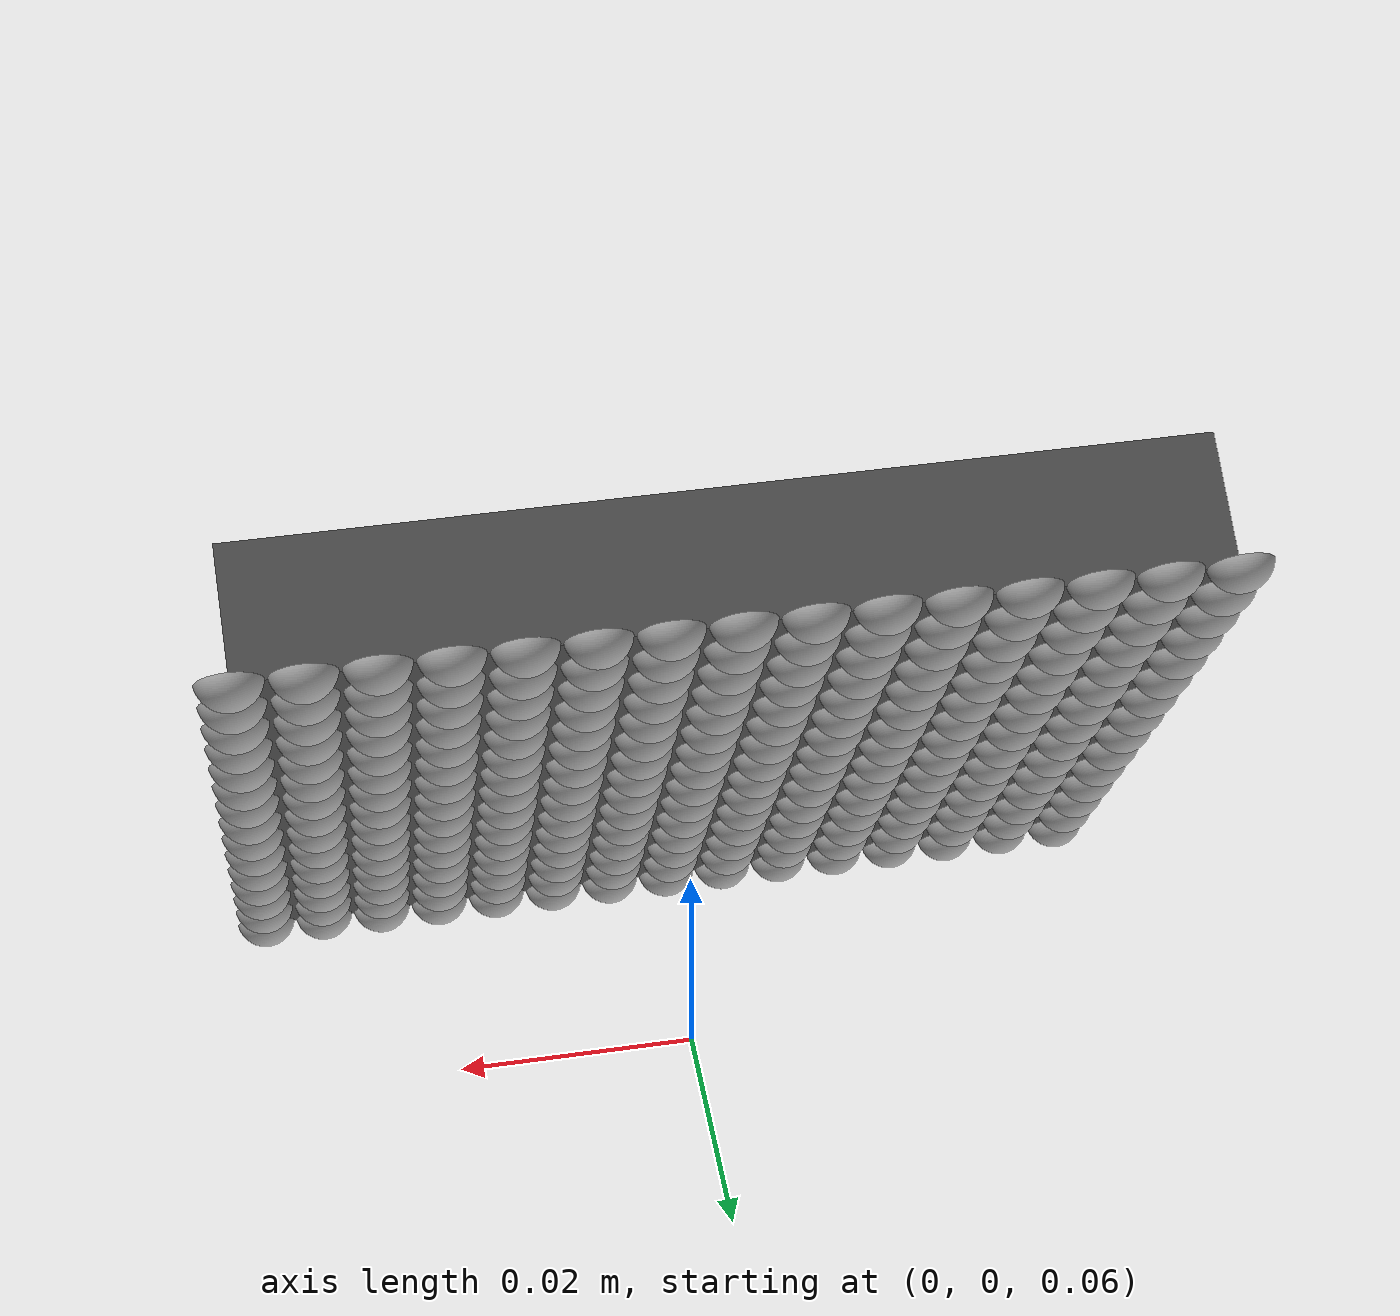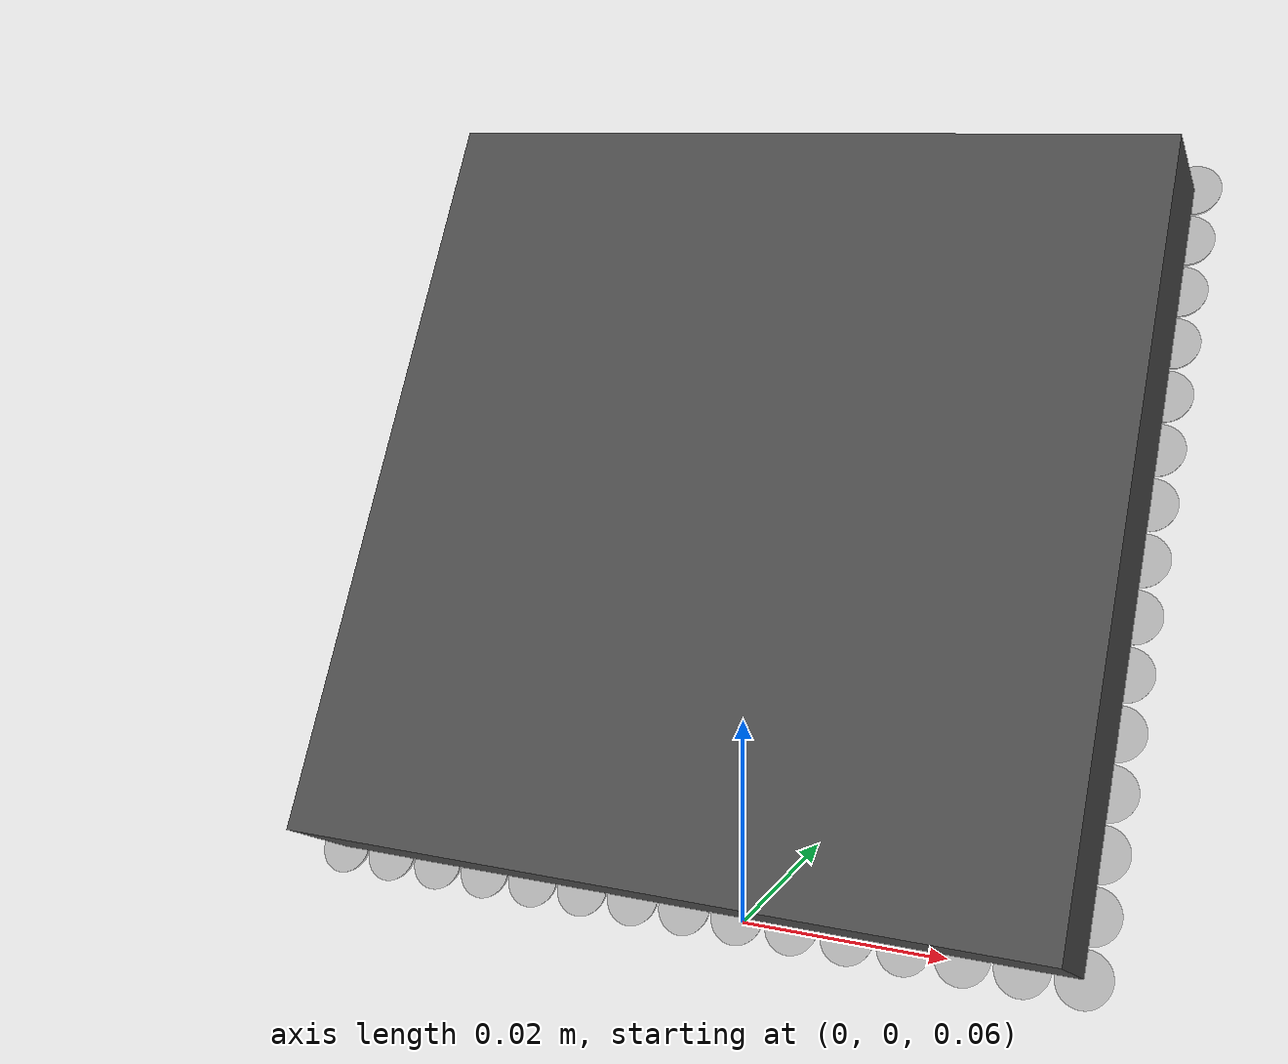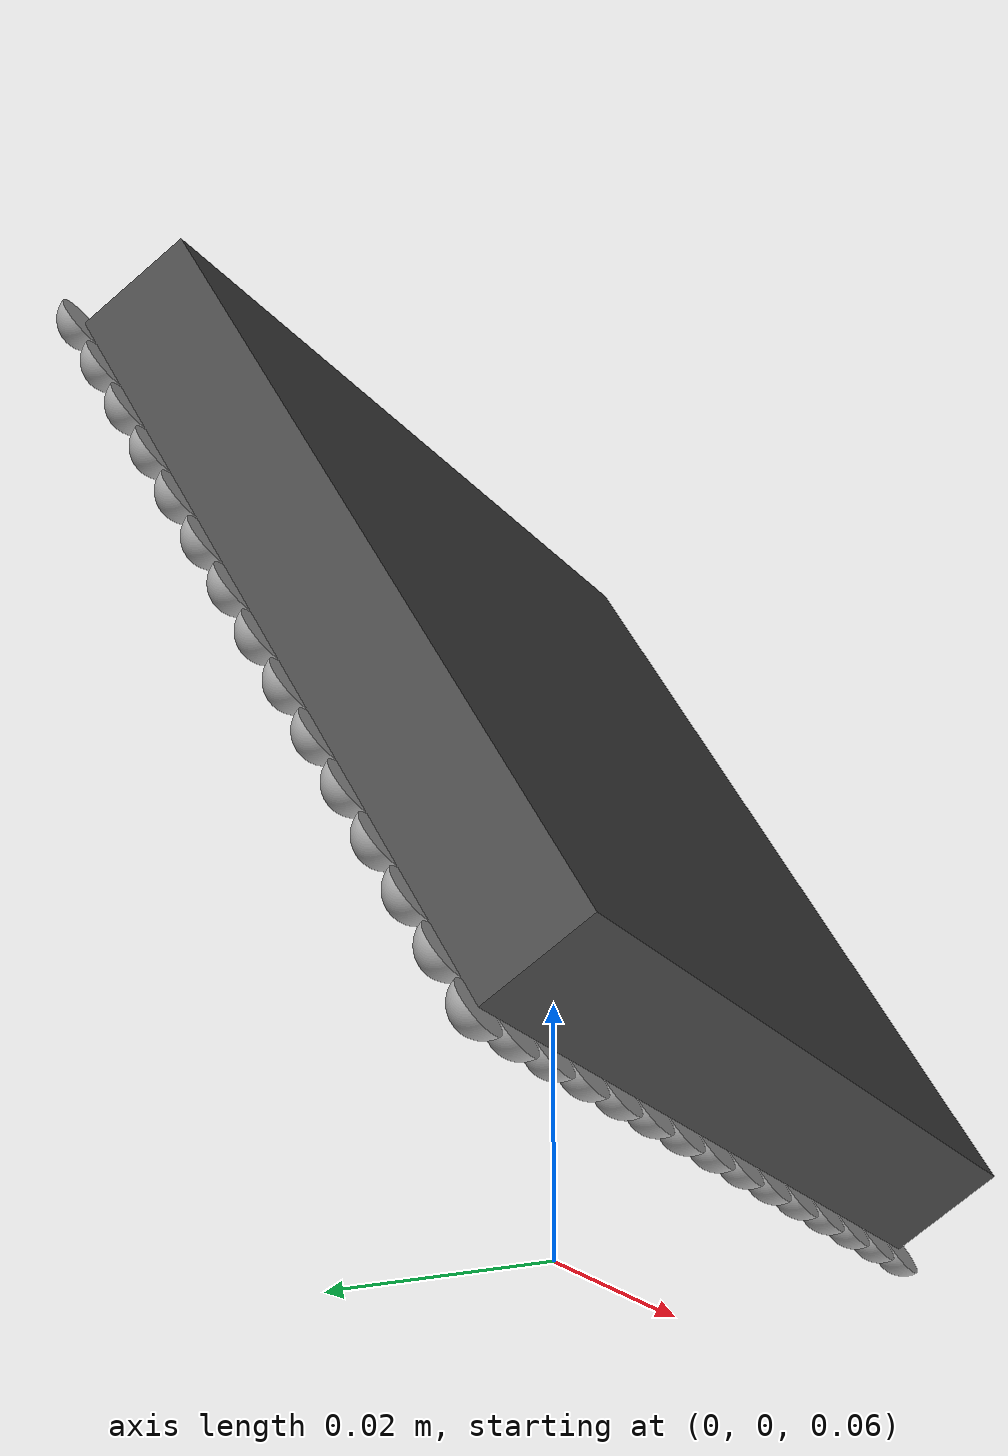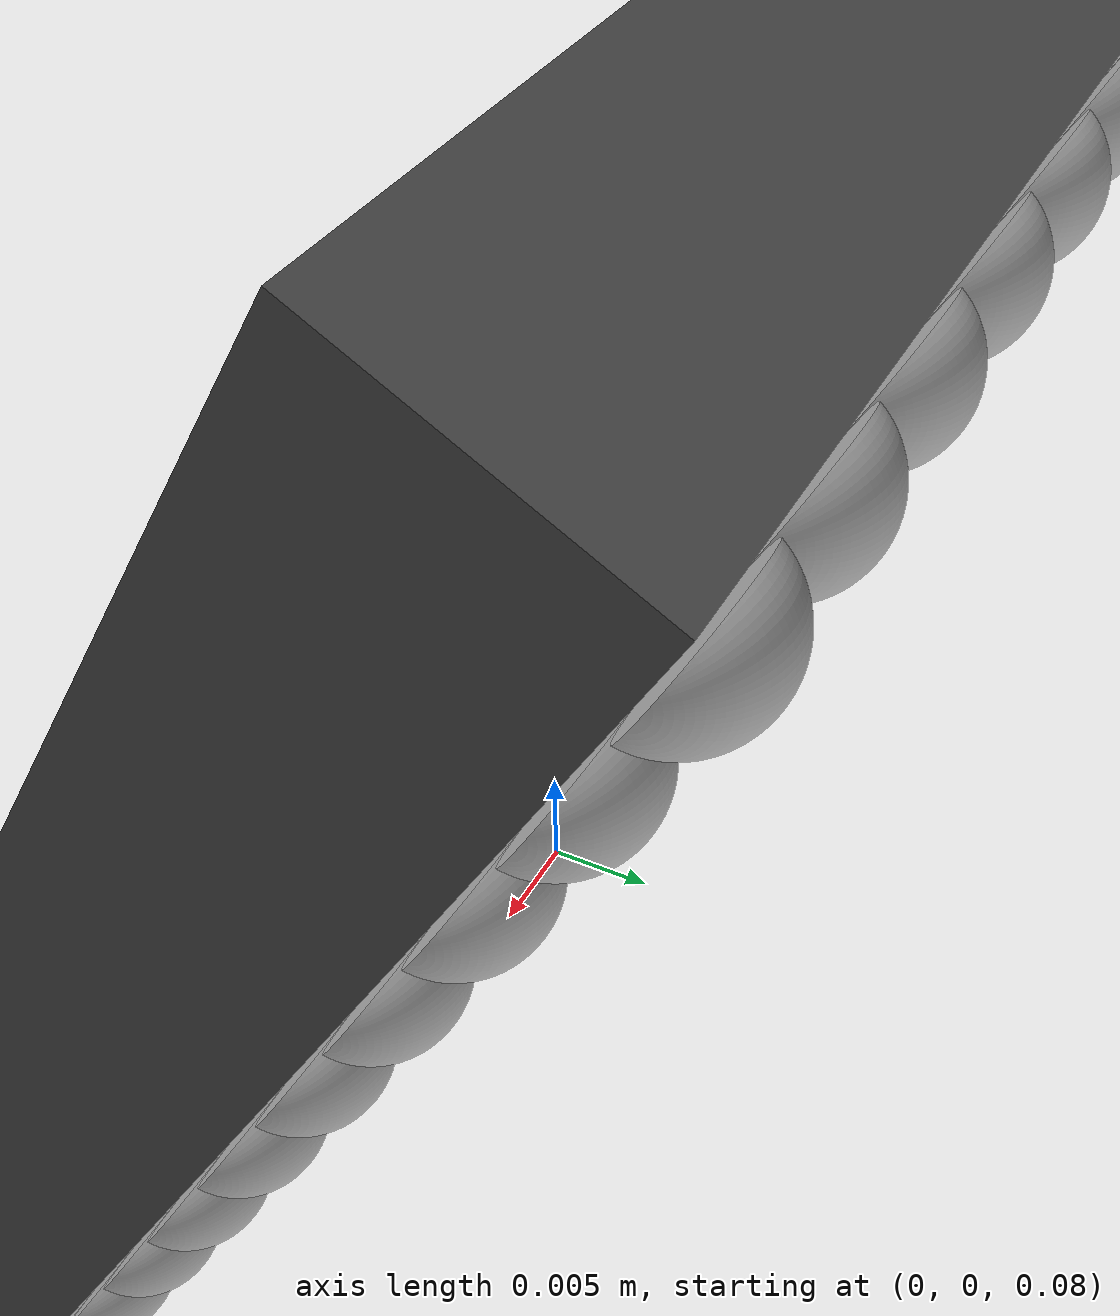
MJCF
<?xml version="1.0" encoding="utf-8"?>
<mujoco>
    <compiler angle="radian" coordinate="local" meshdir="../stls/hand" texturedir="../textures"></compiler>
    <option timestep="0.002" iterations="20" apirate="200">
        <flag warmstart="enable"></flag>
    </option>

    <include file="assets/shared.xml"></include>

    <asset>
        <include file="assets/shared_asset.xml"></include>
    </asset>

    <worldbody>
        <include file="assets/desk_multi2.xml"></include>

        <light directional="true" ambient="0.2 0.2 0.2" diffuse="0.8 0.8 0.8" specular="0.3 0.3 0.3" castshadow="false" pos="0 1 4" dir="0 0 -1" name="light0"></light>
    </worldbody>

    <!--ACTUATORS-->
    <actuator>

    </actuator>

</mujoco>

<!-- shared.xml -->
<mujoco>

    <size njmax="5000" nconmax="1000" nuser_jnt="1" nuser_site="1" nuser_tendon="1" nuser_sensor="1" nuser_actuator="16" nstack="600000"></size>

    <visual>
        <map fogstart="3" fogend="5" force="0.1"></map>
        <quality shadowsize="4096"></quality>
    </visual>

    <default>
        <default class="robot0:asset_class">
            <geom friction="1 0.005 0.001" condim="3" margin="0.0005" contype="1" conaffinity="1"></geom>
            <joint limited="true" damping="0.1" armature="0.001" margin="0.01" frictionloss="0.001"></joint>
            <site size="0.005" rgba="0.4 0.9 0.4 1"></site>
            <general ctrllimited="true" forcelimited="true"></general>
        </default>
        <default class="robot0:D_Touch">
            <site type="box" size="0.009 0.004 0.013" pos="0 -0.004 0.018" rgba="0.8 0.8 0.8 0.15" group="4"></site>
        </default>

        <default class="robot0:Palm">
            <geom material="robot0:MatViz" contype="0" conaffinity="0" group="1" type="mesh"></geom>
        </default>

        <default class="robot0:Finger">
            <geom material="robot0:MatViz" contype="0" conaffinity="0" group="1" type="mesh"></geom>
        </default>

        <default class="robot0:Pad">
            <geom material="robot0:MatViz_Pad" contype="0" conaffinity="0" group="1" type="mesh"></geom>
        </default>

        <default class="robot0:Tactile">
            <geom material="robot0:MatViz_Pad" contype="0" conaffinity="0" group="1" type="mesh"></geom>
        </default>

        <default class="robot0:D_Contact">
            <geom material="robot0:MatColl" contype="1" conaffinity="0" group="4" type="mesh"></geom>
        </default>

        <default class="robot0:free">
            <joint type="free" damping="0" armature="0" limited="false"></joint>
        </default>

    </default>

</mujoco>

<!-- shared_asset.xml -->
<!-- See LICENSE.md for legal notices. LICENSE.md must be kept together with this file. -->
<mujoco>
    <texture type="skybox" builtin="gradient" rgb1="0.44 0.85 0.56" rgb2="0.46 0.87 0.58" width="32" height="32"></texture>

    <texture name="robot0:texplane" type="2d" builtin="checker" rgb1="0.2 0.3 0.4" rgb2="0.1 0.15 0.2" width="512" height="512"></texture>
    <texture name="robot0:texgeom" type="cube" builtin="flat" mark="cross" width="127" height="127" rgb1="0.3 0.6 0.5" rgb2="0.3 0.6 0.5" markrgb="0 0 0" random="0.01"></texture>

    <material name="robot0:MatGnd" reflectance="0.5" texture="robot0:texplane" texrepeat="1 1" texuniform="true"></material>
    <material name="robot0:MatColl" specular="1" shininess="0.3" reflectance="0.5" rgba="0.4 0.5 0.6 1"></material>
    <material name="robot0:MatViz" specular="0.75" shininess="0.1" reflectance="0.5" rgba="0.3 0.3 0.3 1"></material>
    <material name="robot0:MatViz_Pad" specular="0.75" shininess="0.1" reflectance="0.5" rgba="0.7 0.7 0.7 1"></material>

    <material name="object1" specular="0.75" shininess="0.1" reflectance="0.5" rgba="0.7 0.7 0.7 1"></material>
    <material name="object2" specular="0.75" shininess="0.1" reflectance="0.5" rgba="0.3 0.5 0.7 1"></material>

    <material name="robot0:object" texture="robot0:texgeom" texuniform="false"></material>
    <material name="floor_mat" specular="0" shininess="0.5" reflectance="0" rgba="0.2 0.2 0.2 0"></material>

    <mesh name="palm"            file="palm.stl"></mesh>
    <mesh name="link_0.0"        file="link_0.0.stl"></mesh>
    <mesh name="link_1.0"        file="link_1.0.stl" />
    <mesh name="link_2.0"         file="link_2.0.stl" />
    <mesh name="link_middle"   scale="0.001 0.001 0.001" file="link_middle.stl"/>
    <mesh name="link_3.0"         file="link_3.0.stl" />
    <mesh name="link_3.0_tip"  scale="0.001 0.001 0.001" file="fingertip_V2_fixed4.stl"/>
    <mesh name="link_12.0"        file="link_12.0_right.stl" />
    <mesh name="link_13.0"        file="link_13.0.stl" />
    <mesh name="link_14.0"        file="link_14.0.stl" />
    <mesh name="link_15.0"        file="link_15.0.stl" />
    <mesh name="link_15.0_tip" scale="0.001 0.001 0.001"  file="fingertip_V2_fixed4.stl"/>
    <mesh name="tactile_sphere1" scale="0.001 0.001 0.001"  file="tactile_sphere.stl"/>
    <mesh name="tactile_sphere2" scale="0.002 0.002 0.002"  file="tactile_sphere.stl"/>

</mujoco>

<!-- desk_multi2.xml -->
<mujoco>
    <body euler="-0.52358 0 1.5708" name="robot0:hand mount" pos="0 0 0.1">
        <inertial diaginertia="0.001 0.001 0.001" mass="0.001" pos="0 0 0" />

        <body name="robot0:palm" pos="0 0 0">
            <inertial diaginertia="1.e-04 1.e-04 1e-04" mass="0.1" pos="0 0 0.0475" />
            <geom class="robot0:Palm" euler="0 1.5708 0" name="robot0:C_palm" size="0.035 0.035 0.005" type="box" />

            <joint axis="1 0 0" name="joint0" pos="0 0 0" type="slide" limited="true" range="-0.1 0.1"/>

            <body name="palm_root_tactile" pos="0 0 0">

            <body euler="0.0 0.0 0" pos="0.005 -0.035 -0.035"><geom class="robot0:D_Contact" friction="0.5 0.5 0.005" mesh="tactile_sphere2" pos="-0.0005 0 0" quat="0.707107 0 0.707107 0" /><geom class="robot0:Tactile" friction="0.5 0.5 0.005" mesh="tactile_sphere2" pos="-0.0005 0 0" quat="0.707107 0 0.707107 0" /></body><body euler="0.0 0.0 0" pos="0.005 -0.035 -0.03"><geom class="robot0:D_Contact" friction="0.5 0.5 0.005" mesh="tactile_sphere2" pos="-0.0005 0 0" quat="0.707107 0 0.707107 0" /><geom class="robot0:Tactile" friction="0.5 0.5 0.005" mesh="tactile_sphere2" pos="-0.0005 0 0" quat="0.707107 0 0.707107 0" /></body><body euler="0.0 0.0 0" pos="0.005 -0.035 -0.025"><geom class="robot0:D_Contact" friction="0.5 0.5 0.005" mesh="tactile_sphere2" pos="-0.0005 0 0" quat="0.707107 0 0.707107 0" /><geom class="robot0:Tactile" friction="0.5 0.5 0.005" mesh="tactile_sphere2" pos="-0.0005 0 0" quat="0.707107 0 0.707107 0" /></body><body euler="0.0 0.0 0" pos="0.005 -0.035 -0.02"><geom class="robot0:D_Contact" friction="0.5 0.5 0.005" mesh="tactile_sphere2" pos="-0.0005 0 0" quat="0.707107 0 0.707107 0" /><geom class="robot0:Tactile" friction="0.5 0.5 0.005" mesh="tactile_sphere2" pos="-0.0005 0 0" quat="0.707107 0 0.707107 0" /></body><body euler="0.0 0.0 0" pos="0.005 -0.035 -0.015"><geom class="robot0:D_Contact" friction="0.5 0.5 0.005" mesh="tactile_sphere2" pos="-0.0005 0 0" quat="0.707107 0 0.707107 0" /><geom class="robot0:Tactile" friction="0.5 0.5 0.005" mesh="tactile_sphere2" pos="-0.0005 0 0" quat="0.707107 0 0.707107 0" /></body><body euler="0.0 0.0 0" pos="0.005 -0.035 -0.01"><geom class="robot0:D_Contact" friction="0.5 0.5 0.005" mesh="tactile_sphere2" pos="-0.0005 0 0" quat="0.707107 0 0.707107 0" /><geom class="robot0:Tactile" friction="0.5 0.5 0.005" mesh="tactile_sphere2" pos="-0.0005 0 0" quat="0.707107 0 0.707107 0" /></body><body euler="0.0 0.0 0" pos="0.005 -0.035 -0.005"><geom class="robot0:D_Contact" friction="0.5 0.5 0.005" mesh="tactile_sphere2" pos="-0.0005 0 0" quat="0.707107 0 0.707107 0" /><geom class="robot0:Tactile" friction="0.5 0.5 0.005" mesh="tactile_sphere2" pos="-0.0005 0 0" quat="0.707107 0 0.707107 0" /></body><body euler="0.0 0.0 0" pos="0.005 -0.035 0.0"><geom class="robot0:D_Contact" friction="0.5 0.5 0.005" mesh="tactile_sphere2" pos="-0.0005 0 0" quat="0.707107 0 0.707107 0" /><geom class="robot0:Tactile" friction="0.5 0.5 0.005" mesh="tactile_sphere2" pos="-0.0005 0 0" quat="0.707107 0 0.707107 0" /></body><body euler="0.0 0.0 0" pos="0.005 -0.035 0.005"><geom class="robot0:D_Contact" friction="0.5 0.5 0.005" mesh="tactile_sphere2" pos="-0.0005 0 0" quat="0.707107 0 0.707107 0" /><geom class="robot0:Tactile" friction="0.5 0.5 0.005" mesh="tactile_sphere2" pos="-0.0005 0 0" quat="0.707107 0 0.707107 0" /></body><body euler="0.0 0.0 0" pos="0.005 -0.035 0.01"><geom class="robot0:D_Contact" friction="0.5 0.5 0.005" mesh="tactile_sphere2" pos="-0.0005 0 0" quat="0.707107 0 0.707107 0" /><geom class="robot0:Tactile" friction="0.5 0.5 0.005" mesh="tactile_sphere2" pos="-0.0005 0 0" quat="0.707107 0 0.707107 0" /></body><body euler="0.0 0.0 0" pos="0.005 -0.035 0.015"><geom class="robot0:D_Contact" friction="0.5 0.5 0.005" mesh="tactile_sphere2" pos="-0.0005 0 0" quat="0.707107 0 0.707107 0" /><geom class="robot0:Tactile" friction="0.5 0.5 0.005" mesh="tactile_sphere2" pos="-0.0005 0 0" quat="0.707107 0 0.707107 0" /></body><body euler="0.0 0.0 0" pos="0.005 -0.035 0.02"><geom class="robot0:D_Contact" friction="0.5 0.5 0.005" mesh="tactile_sphere2" pos="-0.0005 0 0" quat="0.707107 0 0.707107 0" /><geom class="robot0:Tactile" friction="0.5 0.5 0.005" mesh="tactile_sphere2" pos="-0.0005 0 0" quat="0.707107 0 0.707107 0" /></body><body euler="0.0 0.0 0" pos="0.005 -0.035 0.025"><geom class="robot0:D_Contact" friction="0.5 0.5 0.005" mesh="tactile_sphere2" pos="-0.0005 0 0" quat="0.707107 0 0.707107 0" /><geom class="robot0:Tactile" friction="0.5 0.5 0.005" mesh="tactile_sphere2" pos="-0.0005 0 0" quat="0.707107 0 0.707107 0" /></body><body euler="0.0 0.0 0" pos="0.005 -0.035 0.03"><geom class="robot0:D_Contact" friction="0.5 0.5 0.005" mesh="tactile_sphere2" pos="-0.0005 0 0" quat="0.707107 0 0.707107 0" /><geom class="robot0:Tactile" friction="0.5 0.5 0.005" mesh="tactile_sphere2" pos="-0.0005 0 0" quat="0.707107 0 0.707107 0" /></body><body euler="0.0 0.0 0" pos="0.005 -0.035 0.035"><geom class="robot0:D_Contact" friction="0.5 0.5 0.005" mesh="tactile_sphere2" pos="-0.0005 0 0" quat="0.707107 0 0.707107 0" /><geom class="robot0:Tactile" friction="0.5 0.5 0.005" mesh="tactile_sphere2" pos="-0.0005 0 0" quat="0.707107 0 0.707107 0" /></body><body euler="0.0 0.0 0" pos="0.005 -0.03 -0.035"><geom class="robot0:D_Contact" friction="0.5 0.5 0.005" mesh="tactile_sphere2" pos="-0.0005 0 0" quat="0.707107 0 0.707107 0" /><geom class="robot0:Tactile" friction="0.5 0.5 0.005" mesh="tactile_sphere2" pos="-0.0005 0 0" quat="0.707107 0 0.707107 0" /></body><body euler="0.0 0.0 0" pos="0.005 -0.03 -0.03"><geom class="robot0:D_Contact" friction="0.5 0.5 0.005" mesh="tactile_sphere2" pos="-0.0005 0 0" quat="0.707107 0 0.707107 0" /><geom class="robot0:Tactile" friction="0.5 0.5 0.005" mesh="tactile_sphere2" pos="-0.0005 0 0" quat="0.707107 0 0.707107 0" /></body><body euler="0.0 0.0 0" pos="0.005 -0.03 -0.025"><geom class="robot0:D_Contact" friction="0.5 0.5 0.005" mesh="tactile_sphere2" pos="-0.0005 0 0" quat="0.707107 0 0.707107 0" /><geom class="robot0:Tactile" friction="0.5 0.5 0.005" mesh="tactile_sphere2" pos="-0.0005 0 0" quat="0.707107 0 0.707107 0" /></body><body euler="0.0 0.0 0" pos="0.005 -0.03 -0.02"><geom class="robot0:D_Contact" friction="0.5 0.5 0.005" mesh="tactile_sphere2" pos="-0.0005 0 0" quat="0.707107 0 0.707107 0" /><geom class="robot0:Tactile" friction="0.5 0.5 0.005" mesh="tactile_sphere2" pos="-0.0005 0 0" quat="0.707107 0 0.707107 0" /></body><body euler="0.0 0.0 0" pos="0.005 -0.03 -0.015"><geom class="robot0:D_Contact" friction="0.5 0.5 0.005" mesh="tactile_sphere2" pos="-0.0005 0 0" quat="0.707107 0 0.707107 0" /><geom class="robot0:Tactile" friction="0.5 0.5 0.005" mesh="tactile_sphere2" pos="-0.0005 0 0" quat="0.707107 0 0.707107 0" /></body><body euler="0.0 0.0 0" pos="0.005 -0.03 -0.01"><geom class="robot0:D_Contact" friction="0.5 0.5 0.005" mesh="tactile_sphere2" pos="-0.0005 0 0" quat="0.707107 0 0.707107 0" /><geom class="robot0:Tactile" friction="0.5 0.5 0.005" mesh="tactile_sphere2" pos="-0.0005 0 0" quat="0.707107 0 0.707107 0" /></body><body euler="0.0 0.0 0" pos="0.005 -0.03 -0.005"><geom class="robot0:D_Contact" friction="0.5 0.5 0.005" mesh="tactile_sphere2" pos="-0.0005 0 0" quat="0.707107 0 0.707107 0" /><geom class="robot0:Tactile" friction="0.5 0.5 0.005" mesh="tactile_sphere2" pos="-0.0005 0 0" quat="0.707107 0 0.707107 0" /></body><body euler="0.0 0.0 0" pos="0.005 -0.03 0.0"><geom class="robot0:D_Contact" friction="0.5 0.5 0.005" mesh="tactile_sphere2" pos="-0.0005 0 0" quat="0.707107 0 0.707107 0" /><geom class="robot0:Tactile" friction="0.5 0.5 0.005" mesh="tactile_sphere2" pos="-0.0005 0 0" quat="0.707107 0 0.707107 0" /></body><body euler="0.0 0.0 0" pos="0.005 -0.03 0.005"><geom class="robot0:D_Contact" friction="0.5 0.5 0.005" mesh="tactile_sphere2" pos="-0.0005 0 0" quat="0.707107 0 0.707107 0" /><geom class="robot0:Tactile" friction="0.5 0.5 0.005" mesh="tactile_sphere2" pos="-0.0005 0 0" quat="0.707107 0 0.707107 0" /></body><body euler="0.0 0.0 0" pos="0.005 -0.03 0.01"><geom class="robot0:D_Contact" friction="0.5 0.5 0.005" mesh="tactile_sphere2" pos="-0.0005 0 0" quat="0.707107 0 0.707107 0" /><geom class="robot0:Tactile" friction="0.5 0.5 0.005" mesh="tactile_sphere2" pos="-0.0005 0 0" quat="0.707107 0 0.707107 0" /></body><body euler="0.0 0.0 0" pos="0.005 -0.03 0.015"><geom class="robot0:D_Contact" friction="0.5 0.5 0.005" mesh="tactile_sphere2" pos="-0.0005 0 0" quat="0.707107 0 0.707107 0" /><geom class="robot0:Tactile" friction="0.5 0.5 0.005" mesh="tactile_sphere2" pos="-0.0005 0 0" quat="0.707107 0 0.707107 0" /></body><body euler="0.0 0.0 0" pos="0.005 -0.03 0.02"><geom class="robot0:D_Contact" friction="0.5 0.5 0.005" mesh="tactile_sphere2" pos="-0.0005 0 0" quat="0.707107 0 0.707107 0" /><geom class="robot0:Tactile" friction="0.5 0.5 0.005" mesh="tactile_sphere2" pos="-0.0005 0 0" quat="0.707107 0 0.707107 0" /></body><body euler="0.0 0.0 0" pos="0.005 -0.03 0.025"><geom class="robot0:D_Contact" friction="0.5 0.5 0.005" mesh="tactile_sphere2" pos="-0.0005 0 0" quat="0.707107 0 0.707107 0" /><geom class="robot0:Tactile" friction="0.5 0.5 0.005" mesh="tactile_sphere2" pos="-0.0005 0 0" quat="0.707107 0 0.707107 0" /></body><body euler="0.0 0.0 0" pos="0.005 -0.03 0.03"><geom class="robot0:D_Contact" friction="0.5 0.5 0.005" mesh="tactile_sphere2" pos="-0.0005 0 0" quat="0.707107 0 0.707107 0" /><geom class="robot0:Tactile" friction="0.5 0.5 0.005" mesh="tactile_sphere2" pos="-0.0005 0 0" quat="0.707107 0 0.707107 0" /></body><body euler="0.0 0.0 0" pos="0.005 -0.03 0.035"><geom class="robot0:D_Contact" friction="0.5 0.5 0.005" mesh="tactile_sphere2" pos="-0.0005 0 0" quat="0.707107 0 0.707107 0" /><geom class="robot0:Tactile" friction="0.5 0.5 0.005" mesh="tactile_sphere2" pos="-0.0005 0 0" quat="0.707107 0 0.707107 0" /></body><body euler="0.0 0.0 0" pos="0.005 -0.025 -0.035"><geom class="robot0:D_Contact" friction="0.5 0.5 0.005" mesh="tactile_sphere2" pos="-0.0005 0 0" quat="0.707107 0 0.707107 0" /><geom class="robot0:Tactile" friction="0.5 0.5 0.005" mesh="tactile_sphere2" pos="-0.0005 0 0" quat="0.707107 0 0.707107 0" /></body><body euler="0.0 0.0 0" pos="0.005 -0.025 -0.03"><geom class="robot0:D_Contact" friction="0.5 0.5 0.005" mesh="tactile_sphere2" pos="-0.0005 0 0" quat="0.707107 0 0.707107 0" /><geom class="robot0:Tactile" friction="0.5 0.5 0.005" mesh="tactile_sphere2" pos="-0.0005 0 0" quat="0.707107 0 0.707107 0" /></body><body euler="0.0 0.0 0" pos="0.005 -0.025 -0.025"><geom class="robot0:D_Contact" friction="0.5 0.5 0.005" mesh="tactile_sphere2" pos="-0.0005 0 0" quat="0.707107 0 0.707107 0" /><geom class="robot0:Tactile" friction="0.5 0.5 0.005" mesh="tactile_sphere2" pos="-0.0005 0 0" quat="0.707107 0 0.707107 0" /></body><body euler="0.0 0.0 0" pos="0.005 -0.025 -0.02"><geom class="robot0:D_Contact" friction="0.5 0.5 0.005" mesh="tactile_sphere2" pos="-0.0005 0 0" quat="0.707107 0 0.707107 0" /><geom class="robot0:Tactile" friction="0.5 0.5 0.005" mesh="tactile_sphere2" pos="-0.0005 0 0" quat="0.707107 0 0.707107 0" /></body><body euler="0.0 0.0 0" pos="0.005 -0.025 -0.015"><geom class="robot0:D_Contact" friction="0.5 0.5 0.005" mesh="tactile_sphere2" pos="-0.0005 0 0" quat="0.707107 0 0.707107 0" /><geom class="robot0:Tactile" friction="0.5 0.5 0.005" mesh="tactile_sphere2" pos="-0.0005 0 0" quat="0.707107 0 0.707107 0" /></body><body euler="0.0 0.0 0" pos="0.005 -0.025 -0.01"><geom class="robot0:D_Contact" friction="0.5 0.5 0.005" mesh="tactile_sphere2" pos="-0.0005 0 0" quat="0.707107 0 0.707107 0" /><geom class="robot0:Tactile" friction="0.5 0.5 0.005" mesh="tactile_sphere2" pos="-0.0005 0 0" quat="0.707107 0 0.707107 0" /></body><body euler="0.0 0.0 0" pos="0.005 -0.025 -0.005"><geom class="robot0:D_Contact" friction="0.5 0.5 0.005" mesh="tactile_sphere2" pos="-0.0005 0 0" quat="0.707107 0 0.707107 0" /><geom class="robot0:Tactile" friction="0.5 0.5 0.005" mesh="tactile_sphere2" pos="-0.0005 0 0" quat="0.707107 0 0.707107 0" /></body><body euler="0.0 0.0 0" pos="0.005 -0.025 0.0"><geom class="robot0:D_Contact" friction="0.5 0.5 0.005" mesh="tactile_sphere2" pos="-0.0005 0 0" quat="0.707107 0 0.707107 0" /><geom class="robot0:Tactile" friction="0.5 0.5 0.005" mesh="tactile_sphere2" pos="-0.0005 0 0" quat="0.707107 0 0.707107 0" /></body><body euler="0.0 0.0 0" pos="0.005 -0.025 0.005"><geom class="robot0:D_Contact" friction="0.5 0.5 0.005" mesh="tactile_sphere2" pos="-0.0005 0 0" quat="0.707107 0 0.707107 0" /><geom class="robot0:Tactile" friction="0.5 0.5 0.005" mesh="tactile_sphere2" pos="-0.0005 0 0" quat="0.707107 0 0.707107 0" /></body><body euler="0.0 0.0 0" pos="0.005 -0.025 0.01"><geom class="robot0:D_Contact" friction="0.5 0.5 0.005" mesh="tactile_sphere2" pos="-0.0005 0 0" quat="0.707107 0 0.707107 0" /><geom class="robot0:Tactile" friction="0.5 0.5 0.005" mesh="tactile_sphere2" pos="-0.0005 0 0" quat="0.707107 0 0.707107 0" /></body><body euler="0.0 0.0 0" pos="0.005 -0.025 0.015"><geom class="robot0:D_Contact" friction="0.5 0.5 0.005" mesh="tactile_sphere2" pos="-0.0005 0 0" quat="0.707107 0 0.707107 0" /><geom class="robot0:Tactile" friction="0.5 0.5 0.005" mesh="tactile_sphere2" pos="-0.0005 0 0" quat="0.707107 0 0.707107 0" /></body><body euler="0.0 0.0 0" pos="0.005 -0.025 0.02"><geom class="robot0:D_Contact" friction="0.5 0.5 0.005" mesh="tactile_sphere2" pos="-0.0005 0 0" quat="0.707107 0 0.707107 0" /><geom class="robot0:Tactile" friction="0.5 0.5 0.005" mesh="tactile_sphere2" pos="-0.0005 0 0" quat="0.707107 0 0.707107 0" /></body><body euler="0.0 0.0 0" pos="0.005 -0.025 0.025"><geom class="robot0:D_Contact" friction="0.5 0.5 0.005" mesh="tactile_sphere2" pos="-0.0005 0 0" quat="0.707107 0 0.707107 0" /><geom class="robot0:Tactile" friction="0.5 0.5 0.005" mesh="tactile_sphere2" pos="-0.0005 0 0" quat="0.707107 0 0.707107 0" /></body><body euler="0.0 0.0 0" pos="0.005 -0.025 0.03"><geom class="robot0:D_Contact" friction="0.5 0.5 0.005" mesh="tactile_sphere2" pos="-0.0005 0 0" quat="0.707107 0 0.707107 0" /><geom class="robot0:Tactile" friction="0.5 0.5 0.005" mesh="tactile_sphere2" pos="-0.0005 0 0" quat="0.707107 0 0.707107 0" /></body><body euler="0.0 0.0 0" pos="0.005 -0.025 0.035"><geom class="robot0:D_Contact" friction="0.5 0.5 0.005" mesh="tactile_sphere2" pos="-0.0005 0 0" quat="0.707107 0 0.707107 0" /><geom class="robot0:Tactile" friction="0.5 0.5 0.005" mesh="tactile_sphere2" pos="-0.0005 0 0" quat="0.707107 0 0.707107 0" /></body><body euler="0.0 0.0 0" pos="0.005 -0.02 -0.035"><geom class="robot0:D_Contact" friction="0.5 0.5 0.005" mesh="tactile_sphere2" pos="-0.0005 0 0" quat="0.707107 0 0.707107 0" /><geom class="robot0:Tactile" friction="0.5 0.5 0.005" mesh="tactile_sphere2" pos="-0.0005 0 0" quat="0.707107 0 0.707107 0" /></body><body euler="0.0 0.0 0" pos="0.005 -0.02 -0.03"><geom class="robot0:D_Contact" friction="0.5 0.5 0.005" mesh="tactile_sphere2" pos="-0.0005 0 0" quat="0.707107 0 0.707107 0" /><geom class="robot0:Tactile" friction="0.5 0.5 0.005" mesh="tactile_sphere2" pos="-0.0005 0 0" quat="0.707107 0 0.707107 0" /></body><body euler="0.0 0.0 0" pos="0.005 -0.02 -0.025"><geom class="robot0:D_Contact" friction="0.5 0.5 0.005" mesh="tactile_sphere2" pos="-0.0005 0 0" quat="0.707107 0 0.707107 0" /><geom class="robot0:Tactile" friction="0.5 0.5 0.005" mesh="tactile_sphere2" pos="-0.0005 0 0" quat="0.707107 0 0.707107 0" /></body><body euler="0.0 0.0 0" pos="0.005 -0.02 -0.02"><geom class="robot0:D_Contact" friction="0.5 0.5 0.005" mesh="tactile_sphere2" pos="-0.0005 0 0" quat="0.707107 0 0.707107 0" /><geom class="robot0:Tactile" friction="0.5 0.5 0.005" mesh="tactile_sphere2" pos="-0.0005 0 0" quat="0.707107 0 0.707107 0" /></body><body euler="0.0 0.0 0" pos="0.005 -0.02 -0.015"><geom class="robot0:D_Contact" friction="0.5 0.5 0.005" mesh="tactile_sphere2" pos="-0.0005 0 0" quat="0.707107 0 0.707107 0" /><geom class="robot0:Tactile" friction="0.5 0.5 0.005" mesh="tactile_sphere2" pos="-0.0005 0 0" quat="0.707107 0 0.707107 0" /></body><body euler="0.0 0.0 0" pos="0.005 -0.02 -0.01"><geom class="robot0:D_Contact" friction="0.5 0.5 0.005" mesh="tactile_sphere2" pos="-0.0005 0 0" quat="0.707107 0 0.707107 0" /><geom class="robot0:Tactile" friction="0.5 0.5 0.005" mesh="tactile_sphere2" pos="-0.0005 0 0" quat="0.707107 0 0.707107 0" /></body><body euler="0.0 0.0 0" pos="0.005 -0.02 -0.005"><geom class="robot0:D_Contact" friction="0.5 0.5 0.005" mesh="tactile_sphere2" pos="-0.0005 0 0" quat="0.707107 0 0.707107 0" /><geom class="robot0:Tactile" friction="0.5 0.5 0.005" mesh="tactile_sphere2" pos="-0.0005 0 0" quat="0.707107 0 0.707107 0" /></body><body euler="0.0 0.0 0" pos="0.005 -0.02 0.0"><geom class="robot0:D_Contact" friction="0.5 0.5 0.005" mesh="tactile_sphere2" pos="-0.0005 0 0" quat="0.707107 0 0.707107 0" /><geom class="robot0:Tactile" friction="0.5 0.5 0.005" mesh="tactile_sphere2" pos="-0.0005 0 0" quat="0.707107 0 0.707107 0" /></body><body euler="0.0 0.0 0" pos="0.005 -0.02 0.005"><geom class="robot0:D_Contact" friction="0.5 0.5 0.005" mesh="tactile_sphere2" pos="-0.0005 0 0" quat="0.707107 0 0.707107 0" /><geom class="robot0:Tactile" friction="0.5 0.5 0.005" mesh="tactile_sphere2" pos="-0.0005 0 0" quat="0.707107 0 0.707107 0" /></body><body euler="0.0 0.0 0" pos="0.005 -0.02 0.01"><geom class="robot0:D_Contact" friction="0.5 0.5 0.005" mesh="tactile_sphere2" pos="-0.0005 0 0" quat="0.707107 0 0.707107 0" /><geom class="robot0:Tactile" friction="0.5 0.5 0.005" mesh="tactile_sphere2" pos="-0.0005 0 0" quat="0.707107 0 0.707107 0" /></body><body euler="0.0 0.0 0" pos="0.005 -0.02 0.015"><geom class="robot0:D_Contact" friction="0.5 0.5 0.005" mesh="tactile_sphere2" pos="-0.0005 0 0" quat="0.707107 0 0.707107 0" /><geom class="robot0:Tactile" friction="0.5 0.5 0.005" mesh="tactile_sphere2" pos="-0.0005 0 0" quat="0.707107 0 0.707107 0" /></body><body euler="0.0 0.0 0" pos="0.005 -0.02 0.02"><geom class="robot0:D_Contact" friction="0.5 0.5 0.005" mesh="tactile_sphere2" pos="-0.0005 0 0" quat="0.707107 0 0.707107 0" /><geom class="robot0:Tactile" friction="0.5 0.5 0.005" mesh="tactile_sphere2" pos="-0.0005 0 0" quat="0.707107 0 0.707107 0" /></body><body euler="0.0 0.0 0" pos="0.005 -0.02 0.025"><geom class="robot0:D_Contact" friction="0.5 0.5 0.005" mesh="tactile_sphere2" pos="-0.0005 0 0" quat="0.707107 0 0.707107 0" /><geom class="robot0:Tactile" friction="0.5 0.5 0.005" mesh="tactile_sphere2" pos="-0.0005 0 0" quat="0.707107 0 0.707107 0" /></body><body euler="0.0 0.0 0" pos="0.005 -0.02 0.03"><geom class="robot0:D_Contact" friction="0.5 0.5 0.005" mesh="tactile_sphere2" pos="-0.0005 0 0" quat="0.707107 0 0.707107 0" /><geom class="robot0:Tactile" friction="0.5 0.5 0.005" mesh="tactile_sphere2" pos="-0.0005 0 0" quat="0.707107 0 0.707107 0" /></body><body euler="0.0 0.0 0" pos="0.005 -0.02 0.035"><geom class="robot0:D_Contact" friction="0.5 0.5 0.005" mesh="tactile_sphere2" pos="-0.0005 0 0" quat="0.707107 0 0.707107 0" /><geom class="robot0:Tactile" friction="0.5 0.5 0.005" mesh="tactile_sphere2" pos="-0.0005 0 0" quat="0.707107 0 0.707107 0" /></body><body euler="0.0 0.0 0" pos="0.005 -0.015 -0.035"><geom class="robot0:D_Contact" friction="0.5 0.5 0.005" mesh="tactile_sphere2" pos="-0.0005 0 0" quat="0.707107 0 0.707107 0" /><geom class="robot0:Tactile" friction="0.5 0.5 0.005" mesh="tactile_sphere2" pos="-0.0005 0 0" quat="0.707107 0 0.707107 0" /></body><body euler="0.0 0.0 0" pos="0.005 -0.015 -0.03"><geom class="robot0:D_Contact" friction="0.5 0.5 0.005" mesh="tactile_sphere2" pos="-0.0005 0 0" quat="0.707107 0 0.707107 0" /><geom class="robot0:Tactile" friction="0.5 0.5 0.005" mesh="tactile_sphere2" pos="-0.0005 0 0" quat="0.707107 0 0.707107 0" /></body><body euler="0.0 0.0 0" pos="0.005 -0.015 -0.025"><geom class="robot0:D_Contact" friction="0.5 0.5 0.005" mesh="tactile_sphere2" pos="-0.0005 0 0" quat="0.707107 0 0.707107 0" /><geom class="robot0:Tactile" friction="0.5 0.5 0.005" mesh="tactile_sphere2" pos="-0.0005 0 0" quat="0.707107 0 0.707107 0" /></body><body euler="0.0 0.0 0" pos="0.005 -0.015 -0.02"><geom class="robot0:D_Contact" friction="0.5 0.5 0.005" mesh="tactile_sphere2" pos="-0.0005 0 0" quat="0.707107 0 0.707107 0" /><geom class="robot0:Tactile" friction="0.5 0.5 0.005" mesh="tactile_sphere2" pos="-0.0005 0 0" quat="0.707107 0 0.707107 0" /></body><body euler="0.0 0.0 0" pos="0.005 -0.015 -0.015"><geom class="robot0:D_Contact" friction="0.5 0.5 0.005" mesh="tactile_sphere2" pos="-0.0005 0 0" quat="0.707107 0 0.707107 0" /><geom class="robot0:Tactile" friction="0.5 0.5 0.005" mesh="tactile_sphere2" pos="-0.0005 0 0" quat="0.707107 0 0.707107 0" /></body><body euler="0.0 0.0 0" pos="0.005 -0.015 -0.01"><geom class="robot0:D_Contact" friction="0.5 0.5 0.005" mesh="tactile_sphere2" pos="-0.0005 0 0" quat="0.707107 0 0.707107 0" /><geom class="robot0:Tactile" friction="0.5 0.5 0.005" mesh="tactile_sphere2" pos="-0.0005 0 0" quat="0.707107 0 0.707107 0" /></body><body euler="0.0 0.0 0" pos="0.005 -0.015 -0.005"><geom class="robot0:D_Contact" friction="0.5 0.5 0.005" mesh="tactile_sphere2" pos="-0.0005 0 0" quat="0.707107 0 0.707107 0" /><geom class="robot0:Tactile" friction="0.5 0.5 0.005" mesh="tactile_sphere2" pos="-0.0005 0 0" quat="0.707107 0 0.707107 0" /></body><body euler="0.0 0.0 0" pos="0.005 -0.015 0.0"><geom class="robot0:D_Contact" friction="0.5 0.5 0.005" mesh="tactile_sphere2" pos="-0.0005 0 0" quat="0.707107 0 0.707107 0" /><geom class="robot0:Tactile" friction="0.5 0.5 0.005" mesh="tactile_sphere2" pos="-0.0005 0 0" quat="0.707107 0 0.707107 0" /></body><body euler="0.0 0.0 0" pos="0.005 -0.015 0.005"><geom class="robot0:D_Contact" friction="0.5 0.5 0.005" mesh="tactile_sphere2" pos="-0.0005 0 0" quat="0.707107 0 0.707107 0" /><geom class="robot0:Tactile" friction="0.5 0.5 0.005" mesh="tactile_sphere2" pos="-0.0005 0 0" quat="0.707107 0 0.707107 0" /></body><body euler="0.0 0.0 0" pos="0.005 -0.015 0.01"><geom class="robot0:D_Contact" friction="0.5 0.5 0.005" mesh="tactile_sphere2" pos="-0.0005 0 0" quat="0.707107 0 0.707107 0" /><geom class="robot0:Tactile" friction="0.5 0.5 0.005" mesh="tactile_sphere2" pos="-0.0005 0 0" quat="0.707107 0 0.707107 0" /></body><body euler="0.0 0.0 0" pos="0.005 -0.015 0.015"><geom class="robot0:D_Contact" friction="0.5 0.5 0.005" mesh="tactile_sphere2" pos="-0.0005 0 0" quat="0.707107 0 0.707107 0" /><geom class="robot0:Tactile" friction="0.5 0.5 0.005" mesh="tactile_sphere2" pos="-0.0005 0 0" quat="0.707107 0 0.707107 0" /></body><body euler="0.0 0.0 0" pos="0.005 -0.015 0.02"><geom class="robot0:D_Contact" friction="0.5 0.5 0.005" mesh="tactile_sphere2" pos="-0.0005 0 0" quat="0.707107 0 0.707107 0" /><geom class="robot0:Tactile" friction="0.5 0.5 0.005" mesh="tactile_sphere2" pos="-0.0005 0 0" quat="0.707107 0 0.707107 0" /></body><body euler="0.0 0.0 0" pos="0.005 -0.015 0.025"><geom class="robot0:D_Contact" friction="0.5 0.5 0.005" mesh="tactile_sphere2" pos="-0.0005 0 0" quat="0.707107 0 0.707107 0" /><geom class="robot0:Tactile" friction="0.5 0.5 0.005" mesh="tactile_sphere2" pos="-0.0005 0 0" quat="0.707107 0 0.707107 0" /></body><body euler="0.0 0.0 0" pos="0.005 -0.015 0.03"><geom class="robot0:D_Contact" friction="0.5 0.5 0.005" mesh="tactile_sphere2" pos="-0.0005 0 0" quat="0.707107 0 0.707107 0" /><geom class="robot0:Tactile" friction="0.5 0.5 0.005" mesh="tactile_sphere2" pos="-0.0005 0 0" quat="0.707107 0 0.707107 0" /></body><body euler="0.0 0.0 0" pos="0.005 -0.015 0.035"><geom class="robot0:D_Contact" friction="0.5 0.5 0.005" mesh="tactile_sphere2" pos="-0.0005 0 0" quat="0.707107 0 0.707107 0" /><geom class="robot0:Tactile" friction="0.5 0.5 0.005" mesh="tactile_sphere2" pos="-0.0005 0 0" quat="0.707107 0 0.707107 0" /></body><body euler="0.0 0.0 0" pos="0.005 -0.01 -0.035"><geom class="robot0:D_Contact" friction="0.5 0.5 0.005" mesh="tactile_sphere2" pos="-0.0005 0 0" quat="0.707107 0 0.707107 0" /><geom class="robot0:Tactile" friction="0.5 0.5 0.005" mesh="tactile_sphere2" pos="-0.0005 0 0" quat="0.707107 0 0.707107 0" /></body><body euler="0.0 0.0 0" pos="0.005 -0.01 -0.03"><geom class="robot0:D_Contact" friction="0.5 0.5 0.005" mesh="tactile_sphere2" pos="-0.0005 0 0" quat="0.707107 0 0.707107 0" /><geom class="robot0:Tactile" friction="0.5 0.5 0.005" mesh="tactile_sphere2" pos="-0.0005 0 0" quat="0.707107 0 0.707107 0" /></body><body euler="0.0 0.0 0" pos="0.005 -0.01 -0.025"><geom class="robot0:D_Contact" friction="0.5 0.5 0.005" mesh="tactile_sphere2" pos="-0.0005 0 0" quat="0.707107 0 0.707107 0" /><geom class="robot0:Tactile" friction="0.5 0.5 0.005" mesh="tactile_sphere2" pos="-0.0005 0 0" quat="0.707107 0 0.707107 0" /></body><body euler="0.0 0.0 0" pos="0.005 -0.01 -0.02"><geom class="robot0:D_Contact" friction="0.5 0.5 0.005" mesh="tactile_sphere2" pos="-0.0005 0 0" quat="0.707107 0 0.707107 0" /><geom class="robot0:Tactile" friction="0.5 0.5 0.005" mesh="tactile_sphere2" pos="-0.0005 0 0" quat="0.707107 0 0.707107 0" /></body><body euler="0.0 0.0 0" pos="0.005 -0.01 -0.015"><geom class="robot0:D_Contact" friction="0.5 0.5 0.005" mesh="tactile_sphere2" pos="-0.0005 0 0" quat="0.707107 0 0.707107 0" /><geom class="robot0:Tactile" friction="0.5 0.5 0.005" mesh="tactile_sphere2" pos="-0.0005 0 0" quat="0.707107 0 0.707107 0" /></body><body euler="0.0 0.0 0" pos="0.005 -0.01 -0.01"><geom class="robot0:D_Contact" friction="0.5 0.5 0.005" mesh="tactile_sphere2" pos="-0.0005 0 0" quat="0.707107 0 0.707107 0" /><geom class="robot0:Tactile" friction="0.5 0.5 0.005" mesh="tactile_sphere2" pos="-0.0005 0 0" quat="0.707107 0 0.707107 0" /></body><body euler="0.0 0.0 0" pos="0.005 -0.01 -0.005"><geom class="robot0:D_Contact" friction="0.5 0.5 0.005" mesh="tactile_sphere2" pos="-0.0005 0 0" quat="0.707107 0 0.707107 0" /><geom class="robot0:Tactile" friction="0.5 0.5 0.005" mesh="tactile_sphere2" pos="-0.0005 0 0" quat="0.707107 0 0.707107 0" /></body><body euler="0.0 0.0 0" pos="0.005 -0.01 0.0"><geom class="robot0:D_Contact" friction="0.5 0.5 0.005" mesh="tactile_sphere2" pos="-0.0005 0 0" quat="0.707107 0 0.707107 0" /><geom class="robot0:Tactile" friction="0.5 0.5 0.005" mesh="tactile_sphere2" pos="-0.0005 0 0" quat="0.707107 0 0.707107 0" /></body><body euler="0.0 0.0 0" pos="0.005 -0.01 0.005"><geom class="robot0:D_Contact" friction="0.5 0.5 0.005" mesh="tactile_sphere2" pos="-0.0005 0 0" quat="0.707107 0 0.707107 0" /><geom class="robot0:Tactile" friction="0.5 0.5 0.005" mesh="tactile_sphere2" pos="-0.0005 0 0" quat="0.707107 0 0.707107 0" /></body><body euler="0.0 0.0 0" pos="0.005 -0.01 0.01"><geom class="robot0:D_Contact" friction="0.5 0.5 0.005" mesh="tactile_sphere2" pos="-0.0005 0 0" quat="0.707107 0 0.707107 0" /><geom class="robot0:Tactile" friction="0.5 0.5 0.005" mesh="tactile_sphere2" pos="-0.0005 0 0" quat="0.707107 0 0.707107 0" /></body><body euler="0.0 0.0 0" pos="0.005 -0.01 0.015"><geom class="robot0:D_Contact" friction="0.5 0.5 0.005" mesh="tactile_sphere2" pos="-0.0005 0 0" quat="0.707107 0 0.707107 0" /><geom class="robot0:Tactile" friction="0.5 0.5 0.005" mesh="tactile_sphere2" pos="-0.0005 0 0" quat="0.707107 0 0.707107 0" /></body><body euler="0.0 0.0 0" pos="0.005 -0.01 0.02"><geom class="robot0:D_Contact" friction="0.5 0.5 0.005" mesh="tactile_sphere2" pos="-0.0005 0 0" quat="0.707107 0 0.707107 0" /><geom class="robot0:Tactile" friction="0.5 0.5 0.005" mesh="tactile_sphere2" pos="-0.0005 0 0" quat="0.707107 0 0.707107 0" /></body><body euler="0.0 0.0 0" pos="0.005 -0.01 0.025"><geom class="robot0:D_Contact" friction="0.5 0.5 0.005" mesh="tactile_sphere2" pos="-0.0005 0 0" quat="0.707107 0 0.707107 0" /><geom class="robot0:Tactile" friction="0.5 0.5 0.005" mesh="tactile_sphere2" pos="-0.0005 0 0" quat="0.707107 0 0.707107 0" /></body><body euler="0.0 0.0 0" pos="0.005 -0.01 0.03"><geom class="robot0:D_Contact" friction="0.5 0.5 0.005" mesh="tactile_sphere2" pos="-0.0005 0 0" quat="0.707107 0 0.707107 0" /><geom class="robot0:Tactile" friction="0.5 0.5 0.005" mesh="tactile_sphere2" pos="-0.0005 0 0" quat="0.707107 0 0.707107 0" /></body><body euler="0.0 0.0 0" pos="0.005 -0.01 0.035"><geom class="robot0:D_Contact" friction="0.5 0.5 0.005" mesh="tactile_sphere2" pos="-0.0005 0 0" quat="0.707107 0 0.707107 0" /><geom class="robot0:Tactile" friction="0.5 0.5 0.005" mesh="tactile_sphere2" pos="-0.0005 0 0" quat="0.707107 0 0.707107 0" /></body><body euler="0.0 0.0 0" pos="0.005 -0.005 -0.035"><geom class="robot0:D_Contact" friction="0.5 0.5 0.005" mesh="tactile_sphere2" pos="-0.0005 0 0" quat="0.707107 0 0.707107 0" /><geom class="robot0:Tactile" friction="0.5 0.5 0.005" mesh="tactile_sphere2" pos="-0.0005 0 0" quat="0.707107 0 0.707107 0" /></body><body euler="0.0 0.0 0" pos="0.005 -0.005 -0.03"><geom class="robot0:D_Contact" friction="0.5 0.5 0.005" mesh="tactile_sphere2" pos="-0.0005 0 0" quat="0.707107 0 0.707107 0" /><geom class="robot0:Tactile" friction="0.5 0.5 0.005" mesh="tactile_sphere2" pos="-0.0005 0 0" quat="0.707107 0 0.707107 0" /></body><body euler="0.0 0.0 0" pos="0.005 -0.005 -0.025"><geom class="robot0:D_Contact" friction="0.5 0.5 0.005" mesh="tactile_sphere2" pos="-0.0005 0 0" quat="0.707107 0 0.707107 0" /><geom class="robot0:Tactile" friction="0.5 0.5 0.005" mesh="tactile_sphere2" pos="-0.0005 0 0" quat="0.707107 0 0.707107 0" /></body><body euler="0.0 0.0 0" pos="0.005 -0.005 -0.02"><geom class="robot0:D_Contact" friction="0.5 0.5 0.005" mesh="tactile_sphere2" pos="-0.0005 0 0" quat="0.707107 0 0.707107 0" /><geom class="robot0:Tactile" friction="0.5 0.5 0.005" mesh="tactile_sphere2" pos="-0.0005 0 0" quat="0.707107 0 0.707107 0" /></body><body euler="0.0 0.0 0" pos="0.005 -0.005 -0.015"><geom class="robot0:D_Contact" friction="0.5 0.5 0.005" mesh="tactile_sphere2" pos="-0.0005 0 0" quat="0.707107 0 0.707107 0" /><geom class="robot0:Tactile" friction="0.5 0.5 0.005" mesh="tactile_sphere2" pos="-0.0005 0 0" quat="0.707107 0 0.707107 0" /></body><body euler="0.0 0.0 0" pos="0.005 -0.005 -0.01"><geom class="robot0:D_Contact" friction="0.5 0.5 0.005" mesh="tactile_sphere2" pos="-0.0005 0 0" quat="0.707107 0 0.707107 0" /><geom class="robot0:Tactile" friction="0.5 0.5 0.005" mesh="tactile_sphere2" pos="-0.0005 0 0" quat="0.707107 0 0.707107 0" /></body><body euler="0.0 0.0 0" pos="0.005 -0.005 -0.005"><geom class="robot0:D_Contact" friction="0.5 0.5 0.005" mesh="tactile_sphere2" pos="-0.0005 0 0" quat="0.707107 0 0.707107 0" /><geom class="robot0:Tactile" friction="0.5 0.5 0.005" mesh="tactile_sphere2" pos="-0.0005 0 0" quat="0.707107 0 0.707107 0" /></body><body euler="0.0 0.0 0" pos="0.005 -0.005 0.0"><geom class="robot0:D_Contact" friction="0.5 0.5 0.005" mesh="tactile_sphere2" pos="-0.0005 0 0" quat="0.707107 0 0.707107 0" /><geom class="robot0:Tactile" friction="0.5 0.5 0.005" mesh="tactile_sphere2" pos="-0.0005 0 0" quat="0.707107 0 0.707107 0" /></body><body euler="0.0 0.0 0" pos="0.005 -0.005 0.005"><geom class="robot0:D_Contact" friction="0.5 0.5 0.005" mesh="tactile_sphere2" pos="-0.0005 0 0" quat="0.707107 0 0.707107 0" /><geom class="robot0:Tactile" friction="0.5 0.5 0.005" mesh="tactile_sphere2" pos="-0.0005 0 0" quat="0.707107 0 0.707107 0" /></body><body euler="0.0 0.0 0" pos="0.005 -0.005 0.01"><geom class="robot0:D_Contact" friction="0.5 0.5 0.005" mesh="tactile_sphere2" pos="-0.0005 0 0" quat="0.707107 0 0.707107 0" /><geom class="robot0:Tactile" friction="0.5 0.5 0.005" mesh="tactile_sphere2" pos="-0.0005 0 0" quat="0.707107 0 0.707107 0" /></body><body euler="0.0 0.0 0" pos="0.005 -0.005 0.015"><geom class="robot0:D_Contact" friction="0.5 0.5 0.005" mesh="tactile_sphere2" pos="-0.0005 0 0" quat="0.707107 0 0.707107 0" /><geom class="robot0:Tactile" friction="0.5 0.5 0.005" mesh="tactile_sphere2" pos="-0.0005 0 0" quat="0.707107 0 0.707107 0" /></body><body euler="0.0 0.0 0" pos="0.005 -0.005 0.02"><geom class="robot0:D_Contact" friction="0.5 0.5 0.005" mesh="tactile_sphere2" pos="-0.0005 0 0" quat="0.707107 0 0.707107 0" /><geom class="robot0:Tactile" friction="0.5 0.5 0.005" mesh="tactile_sphere2" pos="-0.0005 0 0" quat="0.707107 0 0.707107 0" /></body><body euler="0.0 0.0 0" pos="0.005 -0.005 0.025"><geom class="robot0:D_Contact" friction="0.5 0.5 0.005" mesh="tactile_sphere2" pos="-0.0005 0 0" quat="0.707107 0 0.707107 0" /><geom class="robot0:Tactile" friction="0.5 0.5 0.005" mesh="tactile_sphere2" pos="-0.0005 0 0" quat="0.707107 0 0.707107 0" /></body><body euler="0.0 0.0 0" pos="0.005 -0.005 0.03"><geom class="robot0:D_Contact" friction="0.5 0.5 0.005" mesh="tactile_sphere2" pos="-0.0005 0 0" quat="0.707107 0 0.707107 0" /><geom class="robot0:Tactile" friction="0.5 0.5 0.005" mesh="tactile_sphere2" pos="-0.0005 0 0" quat="0.707107 0 0.707107 0" /></body><body euler="0.0 0.0 0" pos="0.005 -0.005 0.035"><geom class="robot0:D_Contact" friction="0.5 0.5 0.005" mesh="tactile_sphere2" pos="-0.0005 0 0" quat="0.707107 0 0.707107 0" /><geom class="robot0:Tactile" friction="0.5 0.5 0.005" mesh="tactile_sphere2" pos="-0.0005 0 0" quat="0.707107 0 0.707107 0" /></body><body euler="0.0 0.0 0" pos="0.005 0.0 -0.035"><geom class="robot0:D_Contact" friction="0.5 0.5 0.005" mesh="tactile_sphere2" pos="-0.0005 0 0" quat="0.707107 0 0.707107 0" /><geom class="robot0:Tactile" friction="0.5 0.5 0.005" mesh="tactile_sphere2" pos="-0.0005 0 0" quat="0.707107 0 0.707107 0" /></body><body euler="0.0 0.0 0" pos="0.005 0.0 -0.03"><geom class="robot0:D_Contact" friction="0.5 0.5 0.005" mesh="tactile_sphere2" pos="-0.0005 0 0" quat="0.707107 0 0.707107 0" /><geom class="robot0:Tactile" friction="0.5 0.5 0.005" mesh="tactile_sphere2" pos="-0.0005 0 0" quat="0.707107 0 0.707107 0" /></body><body euler="0.0 0.0 0" pos="0.005 0.0 -0.025"><geom class="robot0:D_Contact" friction="0.5 0.5 0.005" mesh="tactile_sphere2" pos="-0.0005 0 0" quat="0.707107 0 0.707107 0" /><geom class="robot0:Tactile" friction="0.5 0.5 0.005" mesh="tactile_sphere2" pos="-0.0005 0 0" quat="0.707107 0 0.707107 0" /></body><body euler="0.0 0.0 0" pos="0.005 0.0 -0.02"><geom class="robot0:D_Contact" friction="0.5 0.5 0.005" mesh="tactile_sphere2" pos="-0.0005 0 0" quat="0.707107 0 0.707107 0" /><geom class="robot0:Tactile" friction="0.5 0.5 0.005" mesh="tactile_sphere2" pos="-0.0005 0 0" quat="0.707107 0 0.707107 0" /></body><body euler="0.0 0.0 0" pos="0.005 0.0 -0.015"><geom class="robot0:D_Contact" friction="0.5 0.5 0.005" mesh="tactile_sphere2" pos="-0.0005 0 0" quat="0.707107 0 0.707107 0" /><geom class="robot0:Tactile" friction="0.5 0.5 0.005" mesh="tactile_sphere2" pos="-0.0005 0 0" quat="0.707107 0 0.707107 0" /></body><body euler="0.0 0.0 0" pos="0.005 0.0 -0.01"><geom class="robot0:D_Contact" friction="0.5 0.5 0.005" mesh="tactile_sphere2" pos="-0.0005 0 0" quat="0.707107 0 0.707107 0" /><geom class="robot0:Tactile" friction="0.5 0.5 0.005" mesh="tactile_sphere2" pos="-0.0005 0 0" quat="0.707107 0 0.707107 0" /></body><body euler="0.0 0.0 0" pos="0.005 0.0 -0.005"><geom class="robot0:D_Contact" friction="0.5 0.5 0.005" mesh="tactile_sphere2" pos="-0.0005 0 0" quat="0.707107 0 0.707107 0" /><geom class="robot0:Tactile" friction="0.5 0.5 0.005" mesh="tactile_sphere2" pos="-0.0005 0 0" quat="0.707107 0 0.707107 0" /></body><body euler="0.0 0.0 0" pos="0.005 0.0 0.0"><geom class="robot0:D_Contact" friction="0.5 0.5 0.005" mesh="tactile_sphere2" pos="-0.0005 0 0" quat="0.707107 0 0.707107 0" /><geom class="robot0:Tactile" friction="0.5 0.5 0.005" mesh="tactile_sphere2" pos="-0.0005 0 0" quat="0.707107 0 0.707107 0" /></body><body euler="0.0 0.0 0" pos="0.005 0.0 0.005"><geom class="robot0:D_Contact" friction="0.5 0.5 0.005" mesh="tactile_sphere2" pos="-0.0005 0 0" quat="0.707107 0 0.707107 0" /><geom class="robot0:Tactile" friction="0.5 0.5 0.005" mesh="tactile_sphere2" pos="-0.0005 0 0" quat="0.707107 0 0.707107 0" /></body><body euler="0.0 0.0 0" pos="0.005 0.0 0.01"><geom class="robot0:D_Contact" friction="0.5 0.5 0.005" mesh="tactile_sphere2" pos="-0.0005 0 0" quat="0.707107 0 0.707107 0" /><geom class="robot0:Tactile" friction="0.5 0.5 0.005" mesh="tactile_sphere2" pos="-0.0005 0 0" quat="0.707107 0 0.707107 0" /></body><body euler="0.0 0.0 0" pos="0.005 0.0 0.015"><geom class="robot0:D_Contact" friction="0.5 0.5 0.005" mesh="tactile_sphere2" pos="-0.0005 0 0" quat="0.707107 0 0.707107 0" /><geom class="robot0:Tactile" friction="0.5 0.5 0.005" mesh="tactile_sphere2" pos="-0.0005 0 0" quat="0.707107 0 0.707107 0" /></body><body euler="0.0 0.0 0" pos="0.005 0.0 0.02"><geom class="robot0:D_Contact" friction="0.5 0.5 0.005" mesh="tactile_sphere2" pos="-0.0005 0 0" quat="0.707107 0 0.707107 0" /><geom class="robot0:Tactile" friction="0.5 0.5 0.005" mesh="tactile_sphere2" pos="-0.0005 0 0" quat="0.707107 0 0.707107 0" /></body><body euler="0.0 0.0 0" pos="0.005 0.0 0.025"><geom class="robot0:D_Contact" friction="0.5 0.5 0.005" mesh="tactile_sphere2" pos="-0.0005 0 0" quat="0.707107 0 0.707107 0" /><geom class="robot0:Tactile" friction="0.5 0.5 0.005" mesh="tactile_sphere2" pos="-0.0005 0 0" quat="0.707107 0 0.707107 0" /></body><body euler="0.0 0.0 0" pos="0.005 0.0 0.03"><geom class="robot0:D_Contact" friction="0.5 0.5 0.005" mesh="tactile_sphere2" pos="-0.0005 0 0" quat="0.707107 0 0.707107 0" /><geom class="robot0:Tactile" friction="0.5 0.5 0.005" mesh="tactile_sphere2" pos="-0.0005 0 0" quat="0.707107 0 0.707107 0" /></body><body euler="0.0 0.0 0" pos="0.005 0.0 0.035"><geom class="robot0:D_Contact" friction="0.5 0.5 0.005" mesh="tactile_sphere2" pos="-0.0005 0 0" quat="0.707107 0 0.707107 0" /><geom class="robot0:Tactile" friction="0.5 0.5 0.005" mesh="tactile_sphere2" pos="-0.0005 0 0" quat="0.707107 0 0.707107 0" /></body><body euler="0.0 0.0 0" pos="0.005 0.005 -0.035"><geom class="robot0:D_Contact" friction="0.5 0.5 0.005" mesh="tactile_sphere2" pos="-0.0005 0 0" quat="0.707107 0 0.707107 0" /><geom class="robot0:Tactile" friction="0.5 0.5 0.005" mesh="tactile_sphere2" pos="-0.0005 0 0" quat="0.707107 0 0.707107 0" /></body><body euler="0.0 0.0 0" pos="0.005 0.005 -0.03"><geom class="robot0:D_Contact" friction="0.5 0.5 0.005" mesh="tactile_sphere2" pos="-0.0005 0 0" quat="0.707107 0 0.707107 0" /><geom class="robot0:Tactile" friction="0.5 0.5 0.005" mesh="tactile_sphere2" pos="-0.0005 0 0" quat="0.707107 0 0.707107 0" /></body><body euler="0.0 0.0 0" pos="0.005 0.005 -0.025"><geom class="robot0:D_Contact" friction="0.5 0.5 0.005" mesh="tactile_sphere2" pos="-0.0005 0 0" quat="0.707107 0 0.707107 0" /><geom class="robot0:Tactile" friction="0.5 0.5 0.005" mesh="tactile_sphere2" pos="-0.0005 0 0" quat="0.707107 0 0.707107 0" /></body><body euler="0.0 0.0 0" pos="0.005 0.005 -0.02"><geom class="robot0:D_Contact" friction="0.5 0.5 0.005" mesh="tactile_sphere2" pos="-0.0005 0 0" quat="0.707107 0 0.707107 0" /><geom class="robot0:Tactile" friction="0.5 0.5 0.005" mesh="tactile_sphere2" pos="-0.0005 0 0" quat="0.707107 0 0.707107 0" /></body><body euler="0.0 0.0 0" pos="0.005 0.005 -0.015"><geom class="robot0:D_Contact" friction="0.5 0.5 0.005" mesh="tactile_sphere2" pos="-0.0005 0 0" quat="0.707107 0 0.707107 0" /><geom class="robot0:Tactile" friction="0.5 0.5 0.005" mesh="tactile_sphere2" pos="-0.0005 0 0" quat="0.707107 0 0.707107 0" /></body><body euler="0.0 0.0 0" pos="0.005 0.005 -0.01"><geom class="robot0:D_Contact" friction="0.5 0.5 0.005" mesh="tactile_sphere2" pos="-0.0005 0 0" quat="0.707107 0 0.707107 0" /><geom class="robot0:Tactile" friction="0.5 0.5 0.005" mesh="tactile_sphere2" pos="-0.0005 0 0" quat="0.707107 0 0.707107 0" /></body><body euler="0.0 0.0 0" pos="0.005 0.005 -0.005"><geom class="robot0:D_Contact" friction="0.5 0.5 0.005" mesh="tactile_sphere2" pos="-0.0005 0 0" quat="0.707107 0 0.707107 0" /><geom class="robot0:Tactile" friction="0.5 0.5 0.005" mesh="tactile_sphere2" pos="-0.0005 0 0" quat="0.707107 0 0.707107 0" /></body><body euler="0.0 0.0 0" pos="0.005 0.005 0.0"><geom class="robot0:D_Contact" friction="0.5 0.5 0.005" mesh="tactile_sphere2" pos="-0.0005 0 0" quat="0.707107 0 0.707107 0" /><geom class="robot0:Tactile" friction="0.5 0.5 0.005" mesh="tactile_sphere2" pos="-0.0005 0 0" quat="0.707107 0 0.707107 0" /></body><body euler="0.0 0.0 0" pos="0.005 0.005 0.005"><geom class="robot0:D_Contact" friction="0.5 0.5 0.005" mesh="tactile_sphere2" pos="-0.0005 0 0" quat="0.707107 0 0.707107 0" /><geom class="robot0:Tactile" friction="0.5 0.5 0.005" mesh="tactile_sphere2" pos="-0.0005 0 0" quat="0.707107 0 0.707107 0" /></body><body euler="0.0 0.0 0" pos="0.005 0.005 0.01"><geom class="robot0:D_Contact" friction="0.5 0.5 0.005" mesh="tactile_sphere2" pos="-0.0005 0 0" quat="0.707107 0 0.707107 0" /><geom class="robot0:Tactile" friction="0.5 0.5 0.005" mesh="tactile_sphere2" pos="-0.0005 0 0" quat="0.707107 0 0.707107 0" /></body><body euler="0.0 0.0 0" pos="0.005 0.005 0.015"><geom class="robot0:D_Contact" friction="0.5 0.5 0.005" mesh="tactile_sphere2" pos="-0.0005 0 0" quat="0.707107 0 0.707107 0" /><geom class="robot0:Tactile" friction="0.5 0.5 0.005" mesh="tactile_sphere2" pos="-0.0005 0 0" quat="0.707107 0 0.707107 0" /></body><body euler="0.0 0.0 0" pos="0.005 0.005 0.02"><geom class="robot0:D_Contact" friction="0.5 0.5 0.005" mesh="tactile_sphere2" pos="-0.0005 0 0" quat="0.707107 0 0.707107 0" /><geom class="robot0:Tactile" friction="0.5 0.5 0.005" mesh="tactile_sphere2" pos="-0.0005 0 0" quat="0.707107 0 0.707107 0" /></body><body euler="0.0 0.0 0" pos="0.005 0.005 0.025"><geom class="robot0:D_Contact" friction="0.5 0.5 0.005" mesh="tactile_sphere2" pos="-0.0005 0 0" quat="0.707107 0 0.707107 0" /><geom class="robot0:Tactile" friction="0.5 0.5 0.005" mesh="tactile_sphere2" pos="-0.0005 0 0" quat="0.707107 0 0.707107 0" /></body><body euler="0.0 0.0 0" pos="0.005 0.005 0.03"><geom class="robot0:D_Contact" friction="0.5 0.5 0.005" mesh="tactile_sphere2" pos="-0.0005 0 0" quat="0.707107 0 0.707107 0" /><geom class="robot0:Tactile" friction="0.5 0.5 0.005" mesh="tactile_sphere2" pos="-0.0005 0 0" quat="0.707107 0 0.707107 0" /></body><body euler="0.0 0.0 0" pos="0.005 0.005 0.035"><geom class="robot0:D_Contact" friction="0.5 0.5 0.005" mesh="tactile_sphere2" pos="-0.0005 0 0" quat="0.707107 0 0.707107 0" /><geom class="robot0:Tactile" friction="0.5 0.5 0.005" mesh="tactile_sphere2" pos="-0.0005 0 0" quat="0.707107 0 0.707107 0" /></body><body euler="0.0 0.0 0" pos="0.005 0.01 -0.035"><geom class="robot0:D_Contact" friction="0.5 0.5 0.005" mesh="tactile_sphere2" pos="-0.0005 0 0" quat="0.707107 0 0.707107 0" /><geom class="robot0:Tactile" friction="0.5 0.5 0.005" mesh="tactile_sphere2" pos="-0.0005 0 0" quat="0.707107 0 0.707107 0" /></body><body euler="0.0 0.0 0" pos="0.005 0.01 -0.03"><geom class="robot0:D_Contact" friction="0.5 0.5 0.005" mesh="tactile_sphere2" pos="-0.0005 0 0" quat="0.707107 0 0.707107 0" /><geom class="robot0:Tactile" friction="0.5 0.5 0.005" mesh="tactile_sphere2" pos="-0.0005 0 0" quat="0.707107 0 0.707107 0" /></body><body euler="0.0 0.0 0" pos="0.005 0.01 -0.025"><geom class="robot0:D_Contact" friction="0.5 0.5 0.005" mesh="tactile_sphere2" pos="-0.0005 0 0" quat="0.707107 0 0.707107 0" /><geom class="robot0:Tactile" friction="0.5 0.5 0.005" mesh="tactile_sphere2" pos="-0.0005 0 0" quat="0.707107 0 0.707107 0" /></body><body euler="0.0 0.0 0" pos="0.005 0.01 -0.02"><geom class="robot0:D_Contact" friction="0.5 0.5 0.005" mesh="tactile_sphere2" pos="-0.0005 0 0" quat="0.707107 0 0.707107 0" /><geom class="robot0:Tactile" friction="0.5 0.5 0.005" mesh="tactile_sphere2" pos="-0.0005 0 0" quat="0.707107 0 0.707107 0" /></body><body euler="0.0 0.0 0" pos="0.005 0.01 -0.015"><geom class="robot0:D_Contact" friction="0.5 0.5 0.005" mesh="tactile_sphere2" pos="-0.0005 0 0" quat="0.707107 0 0.707107 0" /><geom class="robot0:Tactile" friction="0.5 0.5 0.005" mesh="tactile_sphere2" pos="-0.0005 0 0" quat="0.707107 0 0.707107 0" /></body><body euler="0.0 0.0 0" pos="0.005 0.01 -0.01"><geom class="robot0:D_Contact" friction="0.5 0.5 0.005" mesh="tactile_sphere2" pos="-0.0005 0 0" quat="0.707107 0 0.707107 0" /><geom class="robot0:Tactile" friction="0.5 0.5 0.005" mesh="tactile_sphere2" pos="-0.0005 0 0" quat="0.707107 0 0.707107 0" /></body><body euler="0.0 0.0 0" pos="0.005 0.01 -0.005"><geom class="robot0:D_Contact" friction="0.5 0.5 0.005" mesh="tactile_sphere2" pos="-0.0005 0 0" quat="0.707107 0 0.707107 0" /><geom class="robot0:Tactile" friction="0.5 0.5 0.005" mesh="tactile_sphere2" pos="-0.0005 0 0" quat="0.707107 0 0.707107 0" /></body><body euler="0.0 0.0 0" pos="0.005 0.01 0.0"><geom class="robot0:D_Contact" friction="0.5 0.5 0.005" mesh="tactile_sphere2" pos="-0.0005 0 0" quat="0.707107 0 0.707107 0" /><geom class="robot0:Tactile" friction="0.5 0.5 0.005" mesh="tactile_sphere2" pos="-0.0005 0 0" quat="0.707107 0 0.707107 0" /></body><body euler="0.0 0.0 0" pos="0.005 0.01 0.005"><geom class="robot0:D_Contact" friction="0.5 0.5 0.005" mesh="tactile_sphere2" pos="-0.0005 0 0" quat="0.707107 0 0.707107 0" /><geom class="robot0:Tactile" friction="0.5 0.5 0.005" mesh="tactile_sphere2" pos="-0.0005 0 0" quat="0.707107 0 0.707107 0" /></body><body euler="0.0 0.0 0" pos="0.005 0.01 0.01"><geom class="robot0:D_Contact" friction="0.5 0.5 0.005" mesh="tactile_sphere2" pos="-0.0005 0 0" quat="0.707107 0 0.707107 0" /><geom class="robot0:Tactile" friction="0.5 0.5 0.005" mesh="tactile_sphere2" pos="-0.0005 0 0" quat="0.707107 0 0.707107 0" /></body><body euler="0.0 0.0 0" pos="0.005 0.01 0.015"><geom class="robot0:D_Contact" friction="0.5 0.5 0.005" mesh="tactile_sphere2" pos="-0.0005 0 0" quat="0.707107 0 0.707107 0" /><geom class="robot0:Tactile" friction="0.5 0.5 0.005" mesh="tactile_sphere2" pos="-0.0005 0 0" quat="0.707107 0 0.707107 0" /></body><body euler="0.0 0.0 0" pos="0.005 0.01 0.02"><geom class="robot0:D_Contact" friction="0.5 0.5 0.005" mesh="tactile_sphere2" pos="-0.0005 0 0" quat="0.707107 0 0.707107 0" /><geom class="robot0:Tactile" friction="0.5 0.5 0.005" mesh="tactile_sphere2" pos="-0.0005 0 0" quat="0.707107 0 0.707107 0" /></body><body euler="0.0 0.0 0" pos="0.005 0.01 0.025"><geom class="robot0:D_Contact" friction="0.5 0.5 0.005" mesh="tactile_sphere2" pos="-0.0005 0 0" quat="0.707107 0 0.707107 0" /><geom class="robot0:Tactile" friction="0.5 0.5 0.005" mesh="tactile_sphere2" pos="-0.0005 0 0" quat="0.707107 0 0.707107 0" /></body><body euler="0.0 0.0 0" pos="0.005 0.01 0.03"><geom class="robot0:D_Contact" friction="0.5 0.5 0.005" mesh="tactile_sphere2" pos="-0.0005 0 0" quat="0.707107 0 0.707107 0" /><geom class="robot0:Tactile" friction="0.5 0.5 0.005" mesh="tactile_sphere2" pos="-0.0005 0 0" quat="0.707107 0 0.707107 0" /></body><body euler="0.0 0.0 0" pos="0.005 0.01 0.035"><geom class="robot0:D_Contact" friction="0.5 0.5 0.005" mesh="tactile_sphere2" pos="-0.0005 0 0" quat="0.707107 0 0.707107 0" /><geom class="robot0:Tactile" friction="0.5 0.5 0.005" mesh="tactile_sphere2" pos="-0.0005 0 0" quat="0.707107 0 0.707107 0" /></body><body euler="0.0 0.0 0" pos="0.005 0.015 -0.035"><geom class="robot0:D_Contact" friction="0.5 0.5 0.005" mesh="tactile_sphere2" pos="-0.0005 0 0" quat="0.707107 0 0.707107 0" /><geom class="robot0:Tactile" friction="0.5 0.5 0.005" mesh="tactile_sphere2" pos="-0.0005 0 0" quat="0.707107 0 0.707107 0" /></body><body euler="0.0 0.0 0" pos="0.005 0.015 -0.03"><geom class="robot0:D_Contact" friction="0.5 0.5 0.005" mesh="tactile_sphere2" pos="-0.0005 0 0" quat="0.707107 0 0.707107 0" /><geom class="robot0:Tactile" friction="0.5 0.5 0.005" mesh="tactile_sphere2" pos="-0.0005 0 0" quat="0.707107 0 0.707107 0" /></body><body euler="0.0 0.0 0" pos="0.005 0.015 -0.025"><geom class="robot0:D_Contact" friction="0.5 0.5 0.005" mesh="tactile_sphere2" pos="-0.0005 0 0" quat="0.707107 0 0.707107 0" /><geom class="robot0:Tactile" friction="0.5 0.5 0.005" mesh="tactile_sphere2" pos="-0.0005 0 0" quat="0.707107 0 0.707107 0" /></body><body euler="0.0 0.0 0" pos="0.005 0.015 -0.02"><geom class="robot0:D_Contact" friction="0.5 0.5 0.005" mesh="tactile_sphere2" pos="-0.0005 0 0" quat="0.707107 0 0.707107 0" /><geom class="robot0:Tactile" friction="0.5 0.5 0.005" mesh="tactile_sphere2" pos="-0.0005 0 0" quat="0.707107 0 0.707107 0" /></body><body euler="0.0 0.0 0" pos="0.005 0.015 -0.015"><geom class="robot0:D_Contact" friction="0.5 0.5 0.005" mesh="tactile_sphere2" pos="-0.0005 0 0" quat="0.707107 0 0.707107 0" /><geom class="robot0:Tactile" friction="0.5 0.5 0.005" mesh="tactile_sphere2" pos="-0.0005 0 0" quat="0.707107 0 0.707107 0" /></body><body euler="0.0 0.0 0" pos="0.005 0.015 -0.01"><geom class="robot0:D_Contact" friction="0.5 0.5 0.005" mesh="tactile_sphere2" pos="-0.0005 0 0" quat="0.707107 0 0.707107 0" /><geom class="robot0:Tactile" friction="0.5 0.5 0.005" mesh="tactile_sphere2" pos="-0.0005 0 0" quat="0.707107 0 0.707107 0" /></body><body euler="0.0 0.0 0" pos="0.005 0.015 -0.005"><geom class="robot0:D_Contact" friction="0.5 0.5 0.005" mesh="tactile_sphere2" pos="-0.0005 0 0" quat="0.707107 0 0.707107 0" /><geom class="robot0:Tactile" friction="0.5 0.5 0.005" mesh="tactile_sphere2" pos="-0.0005 0 0" quat="0.707107 0 0.707107 0" /></body><body euler="0.0 0.0 0" pos="0.005 0.015 0.0"><geom class="robot0:D_Contact" friction="0.5 0.5 0.005" mesh="tactile_sphere2" pos="-0.0005 0 0" quat="0.707107 0 0.707107 0" /><geom class="robot0:Tactile" friction="0.5 0.5 0.005" mesh="tactile_sphere2" pos="-0.0005 0 0" quat="0.707107 0 0.707107 0" /></body><body euler="0.0 0.0 0" pos="0.005 0.015 0.005"><geom class="robot0:D_Contact" friction="0.5 0.5 0.005" mesh="tactile_sphere2" pos="-0.0005 0 0" quat="0.707107 0 0.707107 0" /><geom class="robot0:Tactile" friction="0.5 0.5 0.005" mesh="tactile_sphere2" pos="-0.0005 0 0" quat="0.707107 0 0.707107 0" /></body><body euler="0.0 0.0 0" pos="0.005 0.015 0.01"><geom class="robot0:D_Contact" friction="0.5 0.5 0.005" mesh="tactile_sphere2" pos="-0.0005 0 0" quat="0.707107 0 0.707107 0" /><geom class="robot0:Tactile" friction="0.5 0.5 0.005" mesh="tactile_sphere2" pos="-0.0005 0 0" quat="0.707107 0 0.707107 0" /></body><body euler="0.0 0.0 0" pos="0.005 0.015 0.015"><geom class="robot0:D_Contact" friction="0.5 0.5 0.005" mesh="tactile_sphere2" pos="-0.0005 0 0" quat="0.707107 0 0.707107 0" /><geom class="robot0:Tactile" friction="0.5 0.5 0.005" mesh="tactile_sphere2" pos="-0.0005 0 0" quat="0.707107 0 0.707107 0" /></body><body euler="0.0 0.0 0" pos="0.005 0.015 0.02"><geom class="robot0:D_Contact" friction="0.5 0.5 0.005" mesh="tactile_sphere2" pos="-0.0005 0 0" quat="0.707107 0 0.707107 0" /><geom class="robot0:Tactile" friction="0.5 0.5 0.005" mesh="tactile_sphere2" pos="-0.0005 0 0" quat="0.707107 0 0.707107 0" /></body><body euler="0.0 0.0 0" pos="0.005 0.015 0.025"><geom class="robot0:D_Contact" friction="0.5 0.5 0.005" mesh="tactile_sphere2" pos="-0.0005 0 0" quat="0.707107 0 0.707107 0" /><geom class="robot0:Tactile" friction="0.5 0.5 0.005" mesh="tactile_sphere2" pos="-0.0005 0 0" quat="0.707107 0 0.707107 0" /></body><body euler="0.0 0.0 0" pos="0.005 0.015 0.03"><geom class="robot0:D_Contact" friction="0.5 0.5 0.005" mesh="tactile_sphere2" pos="-0.0005 0 0" quat="0.707107 0 0.707107 0" /><geom class="robot0:Tactile" friction="0.5 0.5 0.005" mesh="tactile_sphere2" pos="-0.0005 0 0" quat="0.707107 0 0.707107 0" /></body><body euler="0.0 0.0 0" pos="0.005 0.015 0.035"><geom class="robot0:D_Contact" friction="0.5 0.5 0.005" mesh="tactile_sphere2" pos="-0.0005 0 0" quat="0.707107 0 0.707107 0" /><geom class="robot0:Tactile" friction="0.5 0.5 0.005" mesh="tactile_sphere2" pos="-0.0005 0 0" quat="0.707107 0 0.707107 0" /></body><body euler="0.0 0.0 0" pos="0.005 0.02 -0.035"><geom class="robot0:D_Contact" friction="0.5 0.5 0.005" mesh="tactile_sphere2" pos="-0.0005 0 0" quat="0.707107 0 0.707107 0" /><geom class="robot0:Tactile" friction="0.5 0.5 0.005" mesh="tactile_sphere2" pos="-0.0005 0 0" quat="0.707107 0 0.707107 0" /></body><body euler="0.0 0.0 0" pos="0.005 0.02 -0.03"><geom class="robot0:D_Contact" friction="0.5 0.5 0.005" mesh="tactile_sphere2" pos="-0.0005 0 0" quat="0.707107 0 0.707107 0" /><geom class="robot0:Tactile" friction="0.5 0.5 0.005" mesh="tactile_sphere2" pos="-0.0005 0 0" quat="0.707107 0 0.707107 0" /></body><body euler="0.0 0.0 0" pos="0.005 0.02 -0.025"><geom class="robot0:D_Contact" friction="0.5 0.5 0.005" mesh="tactile_sphere2" pos="-0.0005 0 0" quat="0.707107 0 0.707107 0" /><geom class="robot0:Tactile" friction="0.5 0.5 0.005" mesh="tactile_sphere2" pos="-0.0005 0 0" quat="0.707107 0 0.707107 0" /></body><body euler="0.0 0.0 0" pos="0.005 0.02 -0.02"><geom class="robot0:D_Contact" friction="0.5 0.5 0.005" mesh="tactile_sphere2" pos="-0.0005 0 0" quat="0.707107 0 0.707107 0" /><geom class="robot0:Tactile" friction="0.5 0.5 0.005" mesh="tactile_sphere2" pos="-0.0005 0 0" quat="0.707107 0 0.707107 0" /></body><body euler="0.0 0.0 0" pos="0.005 0.02 -0.015"><geom class="robot0:D_Contact" friction="0.5 0.5 0.005" mesh="tactile_sphere2" pos="-0.0005 0 0" quat="0.707107 0 0.707107 0" /><geom class="robot0:Tactile" friction="0.5 0.5 0.005" mesh="tactile_sphere2" pos="-0.0005 0 0" quat="0.707107 0 0.707107 0" /></body><body euler="0.0 0.0 0" pos="0.005 0.02 -0.01"><geom class="robot0:D_Contact" friction="0.5 0.5 0.005" mesh="tactile_sphere2" pos="-0.0005 0 0" quat="0.707107 0 0.707107 0" /><geom class="robot0:Tactile" friction="0.5 0.5 0.005" mesh="tactile_sphere2" pos="-0.0005 0 0" quat="0.707107 0 0.707107 0" /></body><body euler="0.0 0.0 0" pos="0.005 0.02 -0.005"><geom class="robot0:D_Contact" friction="0.5 0.5 0.005" mesh="tactile_sphere2" pos="-0.0005 0 0" quat="0.707107 0 0.707107 0" /><geom class="robot0:Tactile" friction="0.5 0.5 0.005" mesh="tactile_sphere2" pos="-0.0005 0 0" quat="0.707107 0 0.707107 0" /></body><body euler="0.0 0.0 0" pos="0.005 0.02 0.0"><geom class="robot0:D_Contact" friction="0.5 0.5 0.005" mesh="tactile_sphere2" pos="-0.0005 0 0" quat="0.707107 0 0.707107 0" /><geom class="robot0:Tactile" friction="0.5 0.5 0.005" mesh="tactile_sphere2" pos="-0.0005 0 0" quat="0.707107 0 0.707107 0" /></body><body euler="0.0 0.0 0" pos="0.005 0.02 0.005"><geom class="robot0:D_Contact" friction="0.5 0.5 0.005" mesh="tactile_sphere2" pos="-0.0005 0 0" quat="0.707107 0 0.707107 0" /><geom class="robot0:Tactile" friction="0.5 0.5 0.005" mesh="tactile_sphere2" pos="-0.0005 0 0" quat="0.707107 0 0.707107 0" /></body><body euler="0.0 0.0 0" pos="0.005 0.02 0.01"><geom class="robot0:D_Contact" friction="0.5 0.5 0.005" mesh="tactile_sphere2" pos="-0.0005 0 0" quat="0.707107 0 0.707107 0" /><geom class="robot0:Tactile" friction="0.5 0.5 0.005" mesh="tactile_sphere2" pos="-0.0005 0 0" quat="0.707107 0 0.707107 0" /></body><body euler="0.0 0.0 0" pos="0.005 0.02 0.015"><geom class="robot0:D_Contact" friction="0.5 0.5 0.005" mesh="tactile_sphere2" pos="-0.0005 0 0" quat="0.707107 0 0.707107 0" /><geom class="robot0:Tactile" friction="0.5 0.5 0.005" mesh="tactile_sphere2" pos="-0.0005 0 0" quat="0.707107 0 0.707107 0" /></body><body euler="0.0 0.0 0" pos="0.005 0.02 0.02"><geom class="robot0:D_Contact" friction="0.5 0.5 0.005" mesh="tactile_sphere2" pos="-0.0005 0 0" quat="0.707107 0 0.707107 0" /><geom class="robot0:Tactile" friction="0.5 0.5 0.005" mesh="tactile_sphere2" pos="-0.0005 0 0" quat="0.707107 0 0.707107 0" /></body><body euler="0.0 0.0 0" pos="0.005 0.02 0.025"><geom class="robot0:D_Contact" friction="0.5 0.5 0.005" mesh="tactile_sphere2" pos="-0.0005 0 0" quat="0.707107 0 0.707107 0" /><geom class="robot0:Tactile" friction="0.5 0.5 0.005" mesh="tactile_sphere2" pos="-0.0005 0 0" quat="0.707107 0 0.707107 0" /></body><body euler="0.0 0.0 0" pos="0.005 0.02 0.03"><geom class="robot0:D_Contact" friction="0.5 0.5 0.005" mesh="tactile_sphere2" pos="-0.0005 0 0" quat="0.707107 0 0.707107 0" /><geom class="robot0:Tactile" friction="0.5 0.5 0.005" mesh="tactile_sphere2" pos="-0.0005 0 0" quat="0.707107 0 0.707107 0" /></body><body euler="0.0 0.0 0" pos="0.005 0.02 0.035"><geom class="robot0:D_Contact" friction="0.5 0.5 0.005" mesh="tactile_sphere2" pos="-0.0005 0 0" quat="0.707107 0 0.707107 0" /><geom class="robot0:Tactile" friction="0.5 0.5 0.005" mesh="tactile_sphere2" pos="-0.0005 0 0" quat="0.707107 0 0.707107 0" /></body><body euler="0.0 0.0 0" pos="0.005 0.025 -0.035"><geom class="robot0:D_Contact" friction="0.5 0.5 0.005" mesh="tactile_sphere2" pos="-0.0005 0 0" quat="0.707107 0 0.707107 0" /><geom class="robot0:Tactile" friction="0.5 0.5 0.005" mesh="tactile_sphere2" pos="-0.0005 0 0" quat="0.707107 0 0.707107 0" /></body><body euler="0.0 0.0 0" pos="0.005 0.025 -0.03"><geom class="robot0:D_Contact" friction="0.5 0.5 0.005" mesh="tactile_sphere2" pos="-0.0005 0 0" quat="0.707107 0 0.707107 0" /><geom class="robot0:Tactile" friction="0.5 0.5 0.005" mesh="tactile_sphere2" pos="-0.0005 0 0" quat="0.707107 0 0.707107 0" /></body><body euler="0.0 0.0 0" pos="0.005 0.025 -0.025"><geom class="robot0:D_Contact" friction="0.5 0.5 0.005" mesh="tactile_sphere2" pos="-0.0005 0 0" quat="0.707107 0 0.707107 0" /><geom class="robot0:Tactile" friction="0.5 0.5 0.005" mesh="tactile_sphere2" pos="-0.0005 0 0" quat="0.707107 0 0.707107 0" /></body><body euler="0.0 0.0 0" pos="0.005 0.025 -0.02"><geom class="robot0:D_Contact" friction="0.5 0.5 0.005" mesh="tactile_sphere2" pos="-0.0005 0 0" quat="0.707107 0 0.707107 0" /><geom class="robot0:Tactile" friction="0.5 0.5 0.005" mesh="tactile_sphere2" pos="-0.0005 0 0" quat="0.707107 0 0.707107 0" /></body><body euler="0.0 0.0 0" pos="0.005 0.025 -0.015"><geom class="robot0:D_Contact" friction="0.5 0.5 0.005" mesh="tactile_sphere2" pos="-0.0005 0 0" quat="0.707107 0 0.707107 0" /><geom class="robot0:Tactile" friction="0.5 0.5 0.005" mesh="tactile_sphere2" pos="-0.0005 0 0" quat="0.707107 0 0.707107 0" /></body><body euler="0.0 0.0 0" pos="0.005 0.025 -0.01"><geom class="robot0:D_Contact" friction="0.5 0.5 0.005" mesh="tactile_sphere2" pos="-0.0005 0 0" quat="0.707107 0 0.707107 0" /><geom class="robot0:Tactile" friction="0.5 0.5 0.005" mesh="tactile_sphere2" pos="-0.0005 0 0" quat="0.707107 0 0.707107 0" /></body><body euler="0.0 0.0 0" pos="0.005 0.025 -0.005"><geom class="robot0:D_Contact" friction="0.5 0.5 0.005" mesh="tactile_sphere2" pos="-0.0005 0 0" quat="0.707107 0 0.707107 0" /><geom class="robot0:Tactile" friction="0.5 0.5 0.005" mesh="tactile_sphere2" pos="-0.0005 0 0" quat="0.707107 0 0.707107 0" /></body><body euler="0.0 0.0 0" pos="0.005 0.025 0.0"><geom class="robot0:D_Contact" friction="0.5 0.5 0.005" mesh="tactile_sphere2" pos="-0.0005 0 0" quat="0.707107 0 0.707107 0" /><geom class="robot0:Tactile" friction="0.5 0.5 0.005" mesh="tactile_sphere2" pos="-0.0005 0 0" quat="0.707107 0 0.707107 0" /></body><body euler="0.0 0.0 0" pos="0.005 0.025 0.005"><geom class="robot0:D_Contact" friction="0.5 0.5 0.005" mesh="tactile_sphere2" pos="-0.0005 0 0" quat="0.707107 0 0.707107 0" /><geom class="robot0:Tactile" friction="0.5 0.5 0.005" mesh="tactile_sphere2" pos="-0.0005 0 0" quat="0.707107 0 0.707107 0" /></body><body euler="0.0 0.0 0" pos="0.005 0.025 0.01"><geom class="robot0:D_Contact" friction="0.5 0.5 0.005" mesh="tactile_sphere2" pos="-0.0005 0 0" quat="0.707107 0 0.707107 0" /><geom class="robot0:Tactile" friction="0.5 0.5 0.005" mesh="tactile_sphere2" pos="-0.0005 0 0" quat="0.707107 0 0.707107 0" /></body><body euler="0.0 0.0 0" pos="0.005 0.025 0.015"><geom class="robot0:D_Contact" friction="0.5 0.5 0.005" mesh="tactile_sphere2" pos="-0.0005 0 0" quat="0.707107 0 0.707107 0" /><geom class="robot0:Tactile" friction="0.5 0.5 0.005" mesh="tactile_sphere2" pos="-0.0005 0 0" quat="0.707107 0 0.707107 0" /></body><body euler="0.0 0.0 0" pos="0.005 0.025 0.02"><geom class="robot0:D_Contact" friction="0.5 0.5 0.005" mesh="tactile_sphere2" pos="-0.0005 0 0" quat="0.707107 0 0.707107 0" /><geom class="robot0:Tactile" friction="0.5 0.5 0.005" mesh="tactile_sphere2" pos="-0.0005 0 0" quat="0.707107 0 0.707107 0" /></body><body euler="0.0 0.0 0" pos="0.005 0.025 0.025"><geom class="robot0:D_Contact" friction="0.5 0.5 0.005" mesh="tactile_sphere2" pos="-0.0005 0 0" quat="0.707107 0 0.707107 0" /><geom class="robot0:Tactile" friction="0.5 0.5 0.005" mesh="tactile_sphere2" pos="-0.0005 0 0" quat="0.707107 0 0.707107 0" /></body><body euler="0.0 0.0 0" pos="0.005 0.025 0.03"><geom class="robot0:D_Contact" friction="0.5 0.5 0.005" mesh="tactile_sphere2" pos="-0.0005 0 0" quat="0.707107 0 0.707107 0" /><geom class="robot0:Tactile" friction="0.5 0.5 0.005" mesh="tactile_sphere2" pos="-0.0005 0 0" quat="0.707107 0 0.707107 0" /></body><body euler="0.0 0.0 0" pos="0.005 0.025 0.035"><geom class="robot0:D_Contact" friction="0.5 0.5 0.005" mesh="tactile_sphere2" pos="-0.0005 0 0" quat="0.707107 0 0.707107 0" /><geom class="robot0:Tactile" friction="0.5 0.5 0.005" mesh="tactile_sphere2" pos="-0.0005 0 0" quat="0.707107 0 0.707107 0" /></body><body euler="0.0 0.0 0" pos="0.005 0.03 -0.035"><geom class="robot0:D_Contact" friction="0.5 0.5 0.005" mesh="tactile_sphere2" pos="-0.0005 0 0" quat="0.707107 0 0.707107 0" /><geom class="robot0:Tactile" friction="0.5 0.5 0.005" mesh="tactile_sphere2" pos="-0.0005 0 0" quat="0.707107 0 0.707107 0" /></body><body euler="0.0 0.0 0" pos="0.005 0.03 -0.03"><geom class="robot0:D_Contact" friction="0.5 0.5 0.005" mesh="tactile_sphere2" pos="-0.0005 0 0" quat="0.707107 0 0.707107 0" /><geom class="robot0:Tactile" friction="0.5 0.5 0.005" mesh="tactile_sphere2" pos="-0.0005 0 0" quat="0.707107 0 0.707107 0" /></body><body euler="0.0 0.0 0" pos="0.005 0.03 -0.025"><geom class="robot0:D_Contact" friction="0.5 0.5 0.005" mesh="tactile_sphere2" pos="-0.0005 0 0" quat="0.707107 0 0.707107 0" /><geom class="robot0:Tactile" friction="0.5 0.5 0.005" mesh="tactile_sphere2" pos="-0.0005 0 0" quat="0.707107 0 0.707107 0" /></body><body euler="0.0 0.0 0" pos="0.005 0.03 -0.02"><geom class="robot0:D_Contact" friction="0.5 0.5 0.005" mesh="tactile_sphere2" pos="-0.0005 0 0" quat="0.707107 0 0.707107 0" /><geom class="robot0:Tactile" friction="0.5 0.5 0.005" mesh="tactile_sphere2" pos="-0.0005 0 0" quat="0.707107 0 0.707107 0" /></body><body euler="0.0 0.0 0" pos="0.005 0.03 -0.015"><geom class="robot0:D_Contact" friction="0.5 0.5 0.005" mesh="tactile_sphere2" pos="-0.0005 0 0" quat="0.707107 0 0.707107 0" /><geom class="robot0:Tactile" friction="0.5 0.5 0.005" mesh="tactile_sphere2" pos="-0.0005 0 0" quat="0.707107 0 0.707107 0" /></body><body euler="0.0 0.0 0" pos="0.005 0.03 -0.01"><geom class="robot0:D_Contact" friction="0.5 0.5 0.005" mesh="tactile_sphere2" pos="-0.0005 0 0" quat="0.707107 0 0.707107 0" /><geom class="robot0:Tactile" friction="0.5 0.5 0.005" mesh="tactile_sphere2" pos="-0.0005 0 0" quat="0.707107 0 0.707107 0" /></body><body euler="0.0 0.0 0" pos="0.005 0.03 -0.005"><geom class="robot0:D_Contact" friction="0.5 0.5 0.005" mesh="tactile_sphere2" pos="-0.0005 0 0" quat="0.707107 0 0.707107 0" /><geom class="robot0:Tactile" friction="0.5 0.5 0.005" mesh="tactile_sphere2" pos="-0.0005 0 0" quat="0.707107 0 0.707107 0" /></body><body euler="0.0 0.0 0" pos="0.005 0.03 0.0"><geom class="robot0:D_Contact" friction="0.5 0.5 0.005" mesh="tactile_sphere2" pos="-0.0005 0 0" quat="0.707107 0 0.707107 0" /><geom class="robot0:Tactile" friction="0.5 0.5 0.005" mesh="tactile_sphere2" pos="-0.0005 0 0" quat="0.707107 0 0.707107 0" /></body><body euler="0.0 0.0 0" pos="0.005 0.03 0.005"><geom class="robot0:D_Contact" friction="0.5 0.5 0.005" mesh="tactile_sphere2" pos="-0.0005 0 0" quat="0.707107 0 0.707107 0" /><geom class="robot0:Tactile" friction="0.5 0.5 0.005" mesh="tactile_sphere2" pos="-0.0005 0 0" quat="0.707107 0 0.707107 0" /></body><body euler="0.0 0.0 0" pos="0.005 0.03 0.01"><geom class="robot0:D_Contact" friction="0.5 0.5 0.005" mesh="tactile_sphere2" pos="-0.0005 0 0" quat="0.707107 0 0.707107 0" /><geom class="robot0:Tactile" friction="0.5 0.5 0.005" mesh="tactile_sphere2" pos="-0.0005 0 0" quat="0.707107 0 0.707107 0" /></body><body euler="0.0 0.0 0" pos="0.005 0.03 0.015"><geom class="robot0:D_Contact" friction="0.5 0.5 0.005" mesh="tactile_sphere2" pos="-0.0005 0 0" quat="0.707107 0 0.707107 0" /><geom class="robot0:Tactile" friction="0.5 0.5 0.005" mesh="tactile_sphere2" pos="-0.0005 0 0" quat="0.707107 0 0.707107 0" /></body><body euler="0.0 0.0 0" pos="0.005 0.03 0.02"><geom class="robot0:D_Contact" friction="0.5 0.5 0.005" mesh="tactile_sphere2" pos="-0.0005 0 0" quat="0.707107 0 0.707107 0" /><geom class="robot0:Tactile" friction="0.5 0.5 0.005" mesh="tactile_sphere2" pos="-0.0005 0 0" quat="0.707107 0 0.707107 0" /></body><body euler="0.0 0.0 0" pos="0.005 0.03 0.025"><geom class="robot0:D_Contact" friction="0.5 0.5 0.005" mesh="tactile_sphere2" pos="-0.0005 0 0" quat="0.707107 0 0.707107 0" /><geom class="robot0:Tactile" friction="0.5 0.5 0.005" mesh="tactile_sphere2" pos="-0.0005 0 0" quat="0.707107 0 0.707107 0" /></body><body euler="0.0 0.0 0" pos="0.005 0.03 0.03"><geom class="robot0:D_Contact" friction="0.5 0.5 0.005" mesh="tactile_sphere2" pos="-0.0005 0 0" quat="0.707107 0 0.707107 0" /><geom class="robot0:Tactile" friction="0.5 0.5 0.005" mesh="tactile_sphere2" pos="-0.0005 0 0" quat="0.707107 0 0.707107 0" /></body><body euler="0.0 0.0 0" pos="0.005 0.03 0.035"><geom class="robot0:D_Contact" friction="0.5 0.5 0.005" mesh="tactile_sphere2" pos="-0.0005 0 0" quat="0.707107 0 0.707107 0" /><geom class="robot0:Tactile" friction="0.5 0.5 0.005" mesh="tactile_sphere2" pos="-0.0005 0 0" quat="0.707107 0 0.707107 0" /></body><body euler="0.0 0.0 0" pos="0.005 0.035 -0.035"><geom class="robot0:D_Contact" friction="0.5 0.5 0.005" mesh="tactile_sphere2" pos="-0.0005 0 0" quat="0.707107 0 0.707107 0" /><geom class="robot0:Tactile" friction="0.5 0.5 0.005" mesh="tactile_sphere2" pos="-0.0005 0 0" quat="0.707107 0 0.707107 0" /></body><body euler="0.0 0.0 0" pos="0.005 0.035 -0.03"><geom class="robot0:D_Contact" friction="0.5 0.5 0.005" mesh="tactile_sphere2" pos="-0.0005 0 0" quat="0.707107 0 0.707107 0" /><geom class="robot0:Tactile" friction="0.5 0.5 0.005" mesh="tactile_sphere2" pos="-0.0005 0 0" quat="0.707107 0 0.707107 0" /></body><body euler="0.0 0.0 0" pos="0.005 0.035 -0.025"><geom class="robot0:D_Contact" friction="0.5 0.5 0.005" mesh="tactile_sphere2" pos="-0.0005 0 0" quat="0.707107 0 0.707107 0" /><geom class="robot0:Tactile" friction="0.5 0.5 0.005" mesh="tactile_sphere2" pos="-0.0005 0 0" quat="0.707107 0 0.707107 0" /></body><body euler="0.0 0.0 0" pos="0.005 0.035 -0.02"><geom class="robot0:D_Contact" friction="0.5 0.5 0.005" mesh="tactile_sphere2" pos="-0.0005 0 0" quat="0.707107 0 0.707107 0" /><geom class="robot0:Tactile" friction="0.5 0.5 0.005" mesh="tactile_sphere2" pos="-0.0005 0 0" quat="0.707107 0 0.707107 0" /></body><body euler="0.0 0.0 0" pos="0.005 0.035 -0.015"><geom class="robot0:D_Contact" friction="0.5 0.5 0.005" mesh="tactile_sphere2" pos="-0.0005 0 0" quat="0.707107 0 0.707107 0" /><geom class="robot0:Tactile" friction="0.5 0.5 0.005" mesh="tactile_sphere2" pos="-0.0005 0 0" quat="0.707107 0 0.707107 0" /></body><body euler="0.0 0.0 0" pos="0.005 0.035 -0.01"><geom class="robot0:D_Contact" friction="0.5 0.5 0.005" mesh="tactile_sphere2" pos="-0.0005 0 0" quat="0.707107 0 0.707107 0" /><geom class="robot0:Tactile" friction="0.5 0.5 0.005" mesh="tactile_sphere2" pos="-0.0005 0 0" quat="0.707107 0 0.707107 0" /></body><body euler="0.0 0.0 0" pos="0.005 0.035 -0.005"><geom class="robot0:D_Contact" friction="0.5 0.5 0.005" mesh="tactile_sphere2" pos="-0.0005 0 0" quat="0.707107 0 0.707107 0" /><geom class="robot0:Tactile" friction="0.5 0.5 0.005" mesh="tactile_sphere2" pos="-0.0005 0 0" quat="0.707107 0 0.707107 0" /></body><body euler="0.0 0.0 0" pos="0.005 0.035 0.0"><geom class="robot0:D_Contact" friction="0.5 0.5 0.005" mesh="tactile_sphere2" pos="-0.0005 0 0" quat="0.707107 0 0.707107 0" /><geom class="robot0:Tactile" friction="0.5 0.5 0.005" mesh="tactile_sphere2" pos="-0.0005 0 0" quat="0.707107 0 0.707107 0" /></body><body euler="0.0 0.0 0" pos="0.005 0.035 0.005"><geom class="robot0:D_Contact" friction="0.5 0.5 0.005" mesh="tactile_sphere2" pos="-0.0005 0 0" quat="0.707107 0 0.707107 0" /><geom class="robot0:Tactile" friction="0.5 0.5 0.005" mesh="tactile_sphere2" pos="-0.0005 0 0" quat="0.707107 0 0.707107 0" /></body><body euler="0.0 0.0 0" pos="0.005 0.035 0.01"><geom class="robot0:D_Contact" friction="0.5 0.5 0.005" mesh="tactile_sphere2" pos="-0.0005 0 0" quat="0.707107 0 0.707107 0" /><geom class="robot0:Tactile" friction="0.5 0.5 0.005" mesh="tactile_sphere2" pos="-0.0005 0 0" quat="0.707107 0 0.707107 0" /></body><body euler="0.0 0.0 0" pos="0.005 0.035 0.015"><geom class="robot0:D_Contact" friction="0.5 0.5 0.005" mesh="tactile_sphere2" pos="-0.0005 0 0" quat="0.707107 0 0.707107 0" /><geom class="robot0:Tactile" friction="0.5 0.5 0.005" mesh="tactile_sphere2" pos="-0.0005 0 0" quat="0.707107 0 0.707107 0" /></body><body euler="0.0 0.0 0" pos="0.005 0.035 0.02"><geom class="robot0:D_Contact" friction="0.5 0.5 0.005" mesh="tactile_sphere2" pos="-0.0005 0 0" quat="0.707107 0 0.707107 0" /><geom class="robot0:Tactile" friction="0.5 0.5 0.005" mesh="tactile_sphere2" pos="-0.0005 0 0" quat="0.707107 0 0.707107 0" /></body><body euler="0.0 0.0 0" pos="0.005 0.035 0.025"><geom class="robot0:D_Contact" friction="0.5 0.5 0.005" mesh="tactile_sphere2" pos="-0.0005 0 0" quat="0.707107 0 0.707107 0" /><geom class="robot0:Tactile" friction="0.5 0.5 0.005" mesh="tactile_sphere2" pos="-0.0005 0 0" quat="0.707107 0 0.707107 0" /></body><body euler="0.0 0.0 0" pos="0.005 0.035 0.03"><geom class="robot0:D_Contact" friction="0.5 0.5 0.005" mesh="tactile_sphere2" pos="-0.0005 0 0" quat="0.707107 0 0.707107 0" /><geom class="robot0:Tactile" friction="0.5 0.5 0.005" mesh="tactile_sphere2" pos="-0.0005 0 0" quat="0.707107 0 0.707107 0" /></body><body euler="0.0 0.0 0" pos="0.005 0.035 0.035"><geom class="robot0:D_Contact" friction="0.5 0.5 0.005" mesh="tactile_sphere2" pos="-0.0005 0 0" quat="0.707107 0 0.707107 0" /><geom class="robot0:Tactile" friction="0.5 0.5 0.005" mesh="tactile_sphere2" pos="-0.0005 0 0" quat="0.707107 0 0.707107 0" /></body></body>
        </body>
    </body>
</mujoco>
